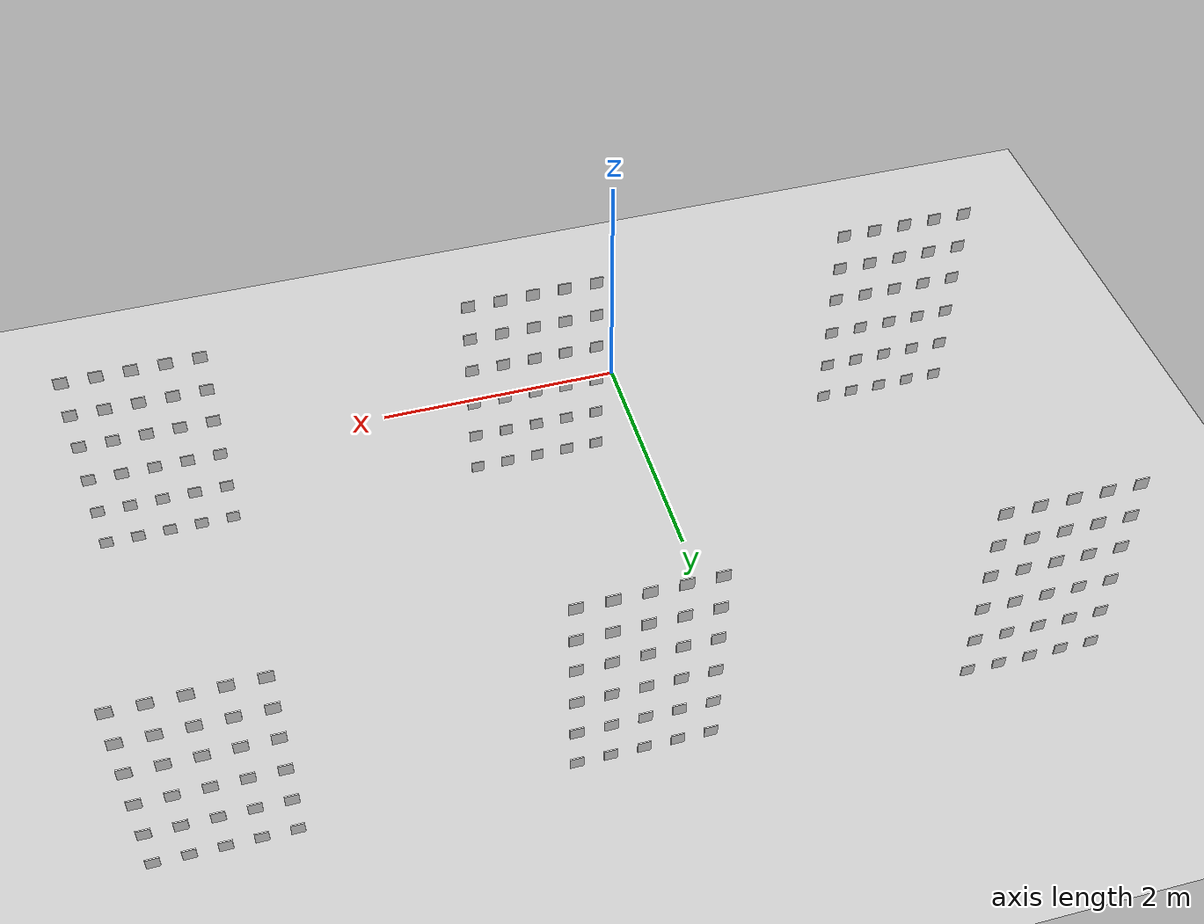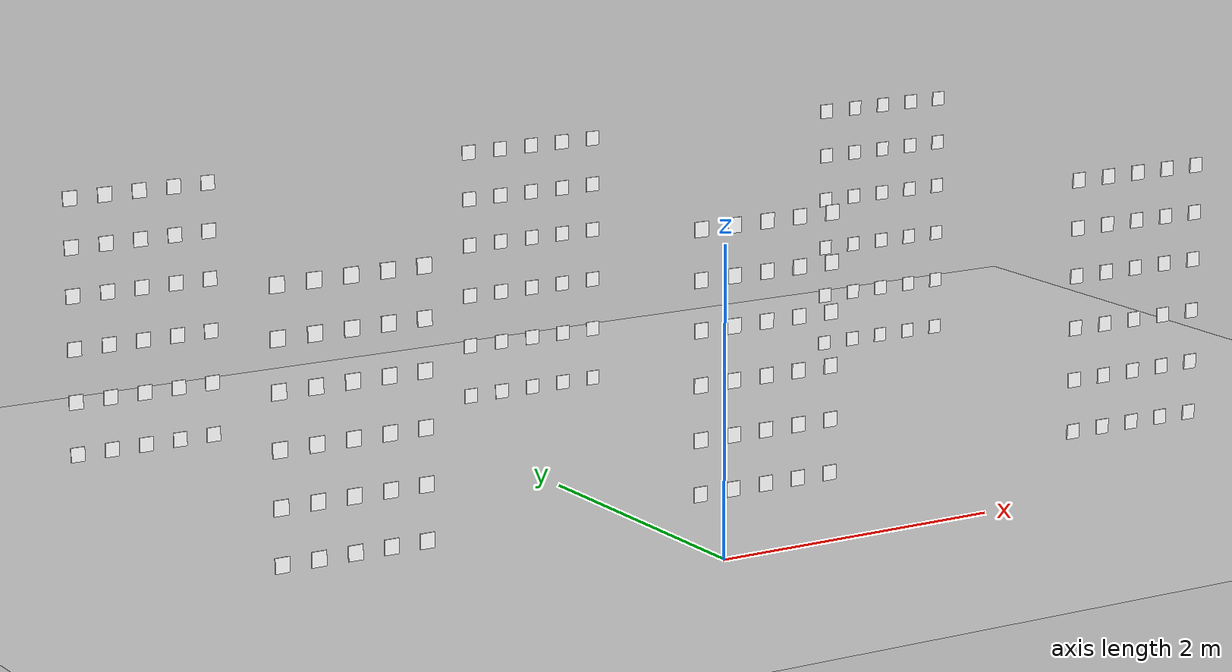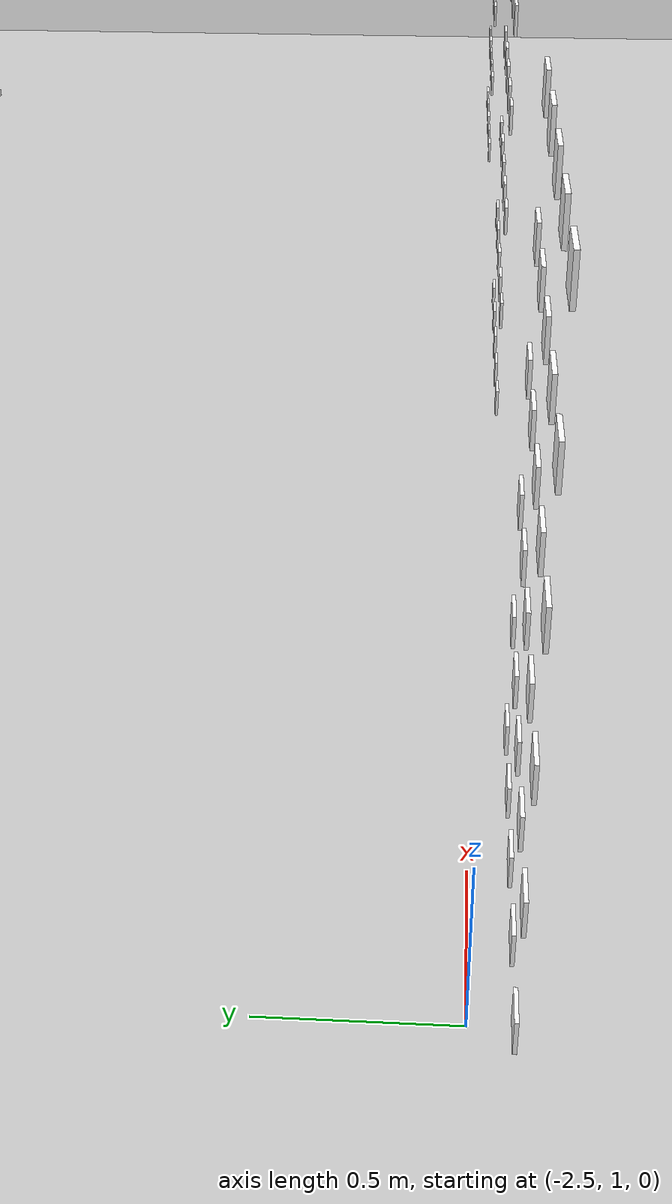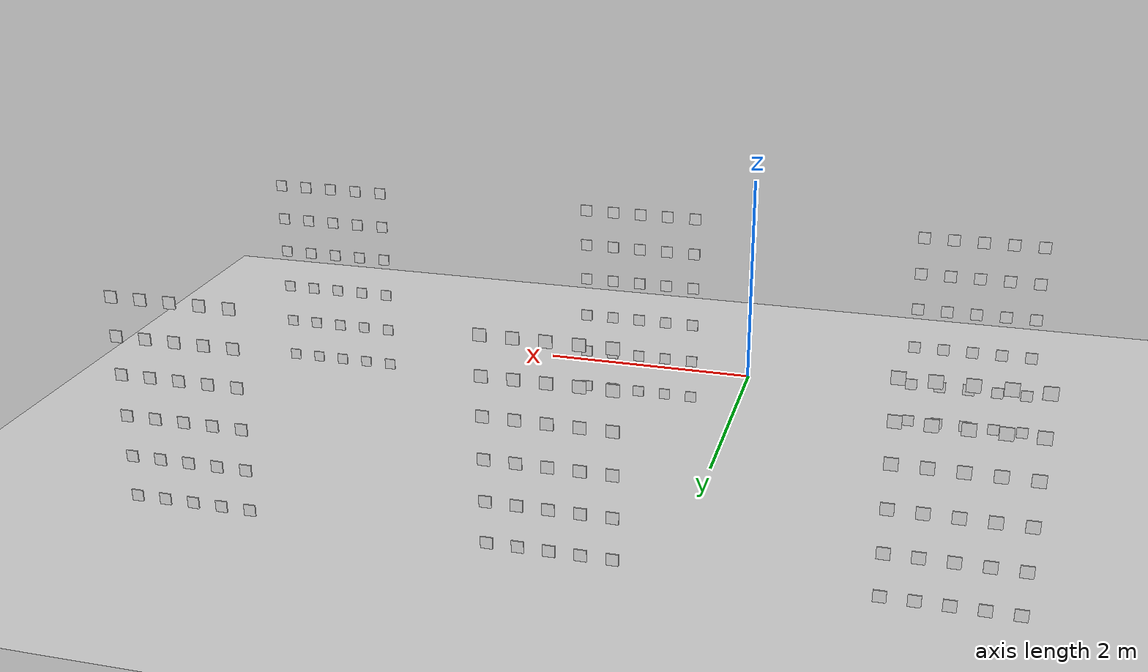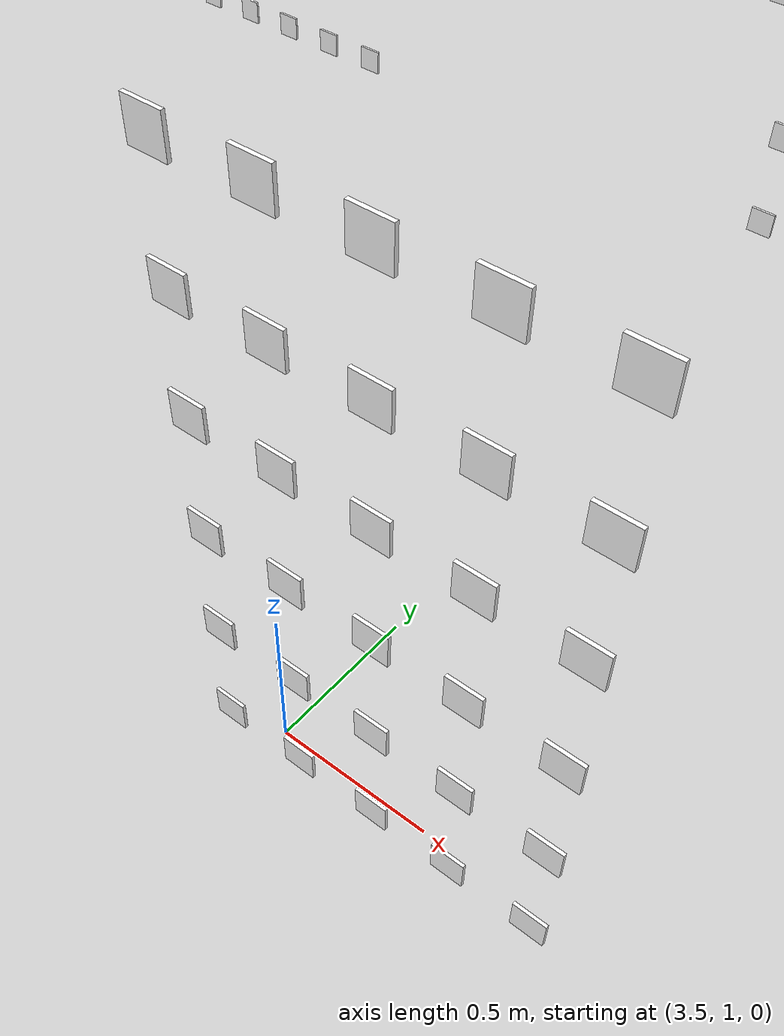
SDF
<sdf version="1.6">
 <world name="default">
  <include><uri>model://ground_plane</uri></include>
  <include><uri>model://sun</uri></include>
  <model name="stag_r1c1_l1_m1">
   <static>true</static>
   <pose>-1.6 0.9 0.146 1.5708 0 0</pose>
   <link name="marker_link">
    <collision name="collision"><geometry><box><size>0.1 0.1 0.01</size></box></geometry></collision>
    <visual name="visual">
     <geometry><box><size>0.1 0.1 0.01</size></box></geometry>
     <material>
      <script>
       <uri>model://STag_marker/materials/scripts</uri>
       <uri>model://STag_marker/materials/textures</uri>
       <name>STagMarker/marker_00219</name>
      </script>
      <ambient>1 1 1 1</ambient>
      <diffuse>1 1 1 1</diffuse>
     </material>
     <pose>0 0 0.001 0 0 0</pose>
    </visual>
   </link>
  </model>
  <model name="stag_r1c1_l1_m2">
   <static>true</static>
   <pose>-1.85 0.9 0.146 1.5708 0 0</pose>
   <link name="marker_link">
    <collision name="collision"><geometry><box><size>0.1 0.1 0.01</size></box></geometry></collision>
    <visual name="visual">
     <geometry><box><size>0.1 0.1 0.01</size></box></geometry>
     <material>
      <script>
       <uri>model://STag_marker/materials/scripts</uri>
       <uri>model://STag_marker/materials/textures</uri>
       <name>STagMarker/marker_00261</name>
      </script>
      <ambient>1 1 1 1</ambient>
      <diffuse>1 1 1 1</diffuse>
     </material>
     <pose>0 0 0.001 0 0 0</pose>
    </visual>
   </link>
  </model>
  <model name="stag_r1c1_l1_m3">
   <static>true</static>
   <pose>-2.1 0.9 0.146 1.5708 0 0</pose>
   <link name="marker_link">
    <collision name="collision"><geometry><box><size>0.1 0.1 0.01</size></box></geometry></collision>
    <visual name="visual">
     <geometry><box><size>0.1 0.1 0.01</size></box></geometry>
     <material>
      <script>
       <uri>model://STag_marker/materials/scripts</uri>
       <uri>model://STag_marker/materials/textures</uri>
       <name>STagMarker/marker_00426</name>
      </script>
      <ambient>1 1 1 1</ambient>
      <diffuse>1 1 1 1</diffuse>
     </material>
     <pose>0 0 0.001 0 0 0</pose>
    </visual>
   </link>
  </model>
  <model name="stag_r1c1_l1_m4">
   <static>true</static>
   <pose>-2.35 0.9 0.146 1.5708 0 0</pose>
   <link name="marker_link">
    <collision name="collision"><geometry><box><size>0.1 0.1 0.01</size></box></geometry></collision>
    <visual name="visual">
     <geometry><box><size>0.1 0.1 0.01</size></box></geometry>
     <material>
      <script>
       <uri>model://STag_marker/materials/scripts</uri>
       <uri>model://STag_marker/materials/textures</uri>
       <name>STagMarker/marker_00519</name>
      </script>
      <ambient>1 1 1 1</ambient>
      <diffuse>1 1 1 1</diffuse>
     </material>
     <pose>0 0 0.001 0 0 0</pose>
    </visual>
   </link>
  </model>
  <model name="stag_r1c1_l1_m5">
   <static>true</static>
   <pose>-2.6 0.9 0.146 1.5708 0 0</pose>
   <link name="marker_link">
    <collision name="collision"><geometry><box><size>0.1 0.1 0.01</size></box></geometry></collision>
    <visual name="visual">
     <geometry><box><size>0.1 0.1 0.01</size></box></geometry>
     <material>
      <script>
       <uri>model://STag_marker/materials/scripts</uri>
       <uri>model://STag_marker/materials/textures</uri>
       <name>STagMarker/marker_00525</name>
      </script>
      <ambient>1 1 1 1</ambient>
      <diffuse>1 1 1 1</diffuse>
     </material>
     <pose>0 0 0.001 0 0 0</pose>
    </visual>
   </link>
  </model>
  <model name="stag_r1c1_l2_m1">
   <static>true</static>
   <pose>-1.6 0.9 0.506 1.5708 0 0</pose>
   <link name="marker_link">
    <collision name="collision"><geometry><box><size>0.1 0.1 0.01</size></box></geometry></collision>
    <visual name="visual">
     <geometry><box><size>0.1 0.1 0.01</size></box></geometry>
     <material>
      <script>
       <uri>model://STag_marker/materials/scripts</uri>
       <uri>model://STag_marker/materials/textures</uri>
       <name>STagMarker/marker_00526</name>
      </script>
      <ambient>1 1 1 1</ambient>
      <diffuse>1 1 1 1</diffuse>
     </material>
     <pose>0 0 0.001 0 0 0</pose>
    </visual>
   </link>
  </model>
  <model name="stag_r1c1_l2_m2">
   <static>true</static>
   <pose>-1.85 0.9 0.506 1.5708 0 0</pose>
   <link name="marker_link">
    <collision name="collision"><geometry><box><size>0.1 0.1 0.01</size></box></geometry></collision>
    <visual name="visual">
     <geometry><box><size>0.1 0.1 0.01</size></box></geometry>
     <material>
      <script>
       <uri>model://STag_marker/materials/scripts</uri>
       <uri>model://STag_marker/materials/textures</uri>
       <name>STagMarker/marker_00537</name>
      </script>
      <ambient>1 1 1 1</ambient>
      <diffuse>1 1 1 1</diffuse>
     </material>
     <pose>0 0 0.001 0 0 0</pose>
    </visual>
   </link>
  </model>
  <model name="stag_r1c1_l2_m3">
   <static>true</static>
   <pose>-2.1 0.9 0.506 1.5708 0 0</pose>
   <link name="marker_link">
    <collision name="collision"><geometry><box><size>0.1 0.1 0.01</size></box></geometry></collision>
    <visual name="visual">
     <geometry><box><size>0.1 0.1 0.01</size></box></geometry>
     <material>
      <script>
       <uri>model://STag_marker/materials/scripts</uri>
       <uri>model://STag_marker/materials/textures</uri>
       <name>STagMarker/marker_00563</name>
      </script>
      <ambient>1 1 1 1</ambient>
      <diffuse>1 1 1 1</diffuse>
     </material>
     <pose>0 0 0.001 0 0 0</pose>
    </visual>
   </link>
  </model>
  <model name="stag_r1c1_l2_m4">
   <static>true</static>
   <pose>-2.35 0.9 0.506 1.5708 0 0</pose>
   <link name="marker_link">
    <collision name="collision"><geometry><box><size>0.1 0.1 0.01</size></box></geometry></collision>
    <visual name="visual">
     <geometry><box><size>0.1 0.1 0.01</size></box></geometry>
     <material>
      <script>
       <uri>model://STag_marker/materials/scripts</uri>
       <uri>model://STag_marker/materials/textures</uri>
       <name>STagMarker/marker_00578</name>
      </script>
      <ambient>1 1 1 1</ambient>
      <diffuse>1 1 1 1</diffuse>
     </material>
     <pose>0 0 0.001 0 0 0</pose>
    </visual>
   </link>
  </model>
  <model name="stag_r1c1_l2_m5">
   <static>true</static>
   <pose>-2.6 0.9 0.506 1.5708 0 0</pose>
   <link name="marker_link">
    <collision name="collision"><geometry><box><size>0.1 0.1 0.01</size></box></geometry></collision>
    <visual name="visual">
     <geometry><box><size>0.1 0.1 0.01</size></box></geometry>
     <material>
      <script>
       <uri>model://STag_marker/materials/scripts</uri>
       <uri>model://STag_marker/materials/textures</uri>
       <name>STagMarker/marker_00679</name>
      </script>
      <ambient>1 1 1 1</ambient>
      <diffuse>1 1 1 1</diffuse>
     </material>
     <pose>0 0 0.001 0 0 0</pose>
    </visual>
   </link>
  </model>
  <model name="stag_r1c1_l3_m1">
   <static>true</static>
   <pose>-1.6 0.9 0.867 1.5708 0 0</pose>
   <link name="marker_link">
    <collision name="collision"><geometry><box><size>0.1 0.1 0.01</size></box></geometry></collision>
    <visual name="visual">
     <geometry><box><size>0.1 0.1 0.01</size></box></geometry>
     <material>
      <script>
       <uri>model://STag_marker/materials/scripts</uri>
       <uri>model://STag_marker/materials/textures</uri>
       <name>STagMarker/marker_00800</name>
      </script>
      <ambient>1 1 1 1</ambient>
      <diffuse>1 1 1 1</diffuse>
     </material>
     <pose>0 0 0.001 0 0 0</pose>
    </visual>
   </link>
  </model>
  <model name="stag_r1c1_l3_m2">
   <static>true</static>
   <pose>-1.85 0.9 0.867 1.5708 0 0</pose>
   <link name="marker_link">
    <collision name="collision"><geometry><box><size>0.1 0.1 0.01</size></box></geometry></collision>
    <visual name="visual">
     <geometry><box><size>0.1 0.1 0.01</size></box></geometry>
     <material>
      <script>
       <uri>model://STag_marker/materials/scripts</uri>
       <uri>model://STag_marker/materials/textures</uri>
       <name>STagMarker/marker_00848</name>
      </script>
      <ambient>1 1 1 1</ambient>
      <diffuse>1 1 1 1</diffuse>
     </material>
     <pose>0 0 0.001 0 0 0</pose>
    </visual>
   </link>
  </model>
  <model name="stag_r1c1_l3_m3">
   <static>true</static>
   <pose>-2.1 0.9 0.867 1.5708 0 0</pose>
   <link name="marker_link">
    <collision name="collision"><geometry><box><size>0.1 0.1 0.01</size></box></geometry></collision>
    <visual name="visual">
     <geometry><box><size>0.1 0.1 0.01</size></box></geometry>
     <material>
      <script>
       <uri>model://STag_marker/materials/scripts</uri>
       <uri>model://STag_marker/materials/textures</uri>
       <name>STagMarker/marker_01138</name>
      </script>
      <ambient>1 1 1 1</ambient>
      <diffuse>1 1 1 1</diffuse>
     </material>
     <pose>0 0 0.001 0 0 0</pose>
    </visual>
   </link>
  </model>
  <model name="stag_r1c1_l3_m4">
   <static>true</static>
   <pose>-2.35 0.9 0.867 1.5708 0 0</pose>
   <link name="marker_link">
    <collision name="collision"><geometry><box><size>0.1 0.1 0.01</size></box></geometry></collision>
    <visual name="visual">
     <geometry><box><size>0.1 0.1 0.01</size></box></geometry>
     <material>
      <script>
       <uri>model://STag_marker/materials/scripts</uri>
       <uri>model://STag_marker/materials/textures</uri>
       <name>STagMarker/marker_01181</name>
      </script>
      <ambient>1 1 1 1</ambient>
      <diffuse>1 1 1 1</diffuse>
     </material>
     <pose>0 0 0.001 0 0 0</pose>
    </visual>
   </link>
  </model>
  <model name="stag_r1c1_l3_m5">
   <static>true</static>
   <pose>-2.6 0.9 0.867 1.5708 0 0</pose>
   <link name="marker_link">
    <collision name="collision"><geometry><box><size>0.1 0.1 0.01</size></box></geometry></collision>
    <visual name="visual">
     <geometry><box><size>0.1 0.1 0.01</size></box></geometry>
     <material>
      <script>
       <uri>model://STag_marker/materials/scripts</uri>
       <uri>model://STag_marker/materials/textures</uri>
       <name>STagMarker/marker_01311</name>
      </script>
      <ambient>1 1 1 1</ambient>
      <diffuse>1 1 1 1</diffuse>
     </material>
     <pose>0 0 0.001 0 0 0</pose>
    </visual>
   </link>
  </model>
  <model name="stag_r1c1_l4_m1">
   <static>true</static>
   <pose>-1.6 0.9 1.227 1.5708 0 0</pose>
   <link name="marker_link">
    <collision name="collision"><geometry><box><size>0.1 0.1 0.01</size></box></geometry></collision>
    <visual name="visual">
     <geometry><box><size>0.1 0.1 0.01</size></box></geometry>
     <material>
      <script>
       <uri>model://STag_marker/materials/scripts</uri>
       <uri>model://STag_marker/materials/textures</uri>
       <name>STagMarker/marker_01391</name>
      </script>
      <ambient>1 1 1 1</ambient>
      <diffuse>1 1 1 1</diffuse>
     </material>
     <pose>0 0 0.001 0 0 0</pose>
    </visual>
   </link>
  </model>
  <model name="stag_r1c1_l4_m2">
   <static>true</static>
   <pose>-1.85 0.9 1.227 1.5708 0 0</pose>
   <link name="marker_link">
    <collision name="collision"><geometry><box><size>0.1 0.1 0.01</size></box></geometry></collision>
    <visual name="visual">
     <geometry><box><size>0.1 0.1 0.01</size></box></geometry>
     <material>
      <script>
       <uri>model://STag_marker/materials/scripts</uri>
       <uri>model://STag_marker/materials/textures</uri>
       <name>STagMarker/marker_01396</name>
      </script>
      <ambient>1 1 1 1</ambient>
      <diffuse>1 1 1 1</diffuse>
     </material>
     <pose>0 0 0.001 0 0 0</pose>
    </visual>
   </link>
  </model>
  <model name="stag_r1c1_l4_m3">
   <static>true</static>
   <pose>-2.1 0.9 1.227 1.5708 0 0</pose>
   <link name="marker_link">
    <collision name="collision"><geometry><box><size>0.1 0.1 0.01</size></box></geometry></collision>
    <visual name="visual">
     <geometry><box><size>0.1 0.1 0.01</size></box></geometry>
     <material>
      <script>
       <uri>model://STag_marker/materials/scripts</uri>
       <uri>model://STag_marker/materials/textures</uri>
       <name>STagMarker/marker_01451</name>
      </script>
      <ambient>1 1 1 1</ambient>
      <diffuse>1 1 1 1</diffuse>
     </material>
     <pose>0 0 0.001 0 0 0</pose>
    </visual>
   </link>
  </model>
  <model name="stag_r1c1_l4_m4">
   <static>true</static>
   <pose>-2.35 0.9 1.227 1.5708 0 0</pose>
   <link name="marker_link">
    <collision name="collision"><geometry><box><size>0.1 0.1 0.01</size></box></geometry></collision>
    <visual name="visual">
     <geometry><box><size>0.1 0.1 0.01</size></box></geometry>
     <material>
      <script>
       <uri>model://STag_marker/materials/scripts</uri>
       <uri>model://STag_marker/materials/textures</uri>
       <name>STagMarker/marker_01509</name>
      </script>
      <ambient>1 1 1 1</ambient>
      <diffuse>1 1 1 1</diffuse>
     </material>
     <pose>0 0 0.001 0 0 0</pose>
    </visual>
   </link>
  </model>
  <model name="stag_r1c1_l4_m5">
   <static>true</static>
   <pose>-2.6 0.9 1.227 1.5708 0 0</pose>
   <link name="marker_link">
    <collision name="collision"><geometry><box><size>0.1 0.1 0.01</size></box></geometry></collision>
    <visual name="visual">
     <geometry><box><size>0.1 0.1 0.01</size></box></geometry>
     <material>
      <script>
       <uri>model://STag_marker/materials/scripts</uri>
       <uri>model://STag_marker/materials/textures</uri>
       <name>STagMarker/marker_01579</name>
      </script>
      <ambient>1 1 1 1</ambient>
      <diffuse>1 1 1 1</diffuse>
     </material>
     <pose>0 0 0.001 0 0 0</pose>
    </visual>
   </link>
  </model>
  <model name="stag_r1c1_l5_m1">
   <static>true</static>
   <pose>-1.6 0.9 1.556 1.5708 0 0</pose>
   <link name="marker_link">
    <collision name="collision"><geometry><box><size>0.1 0.1 0.01</size></box></geometry></collision>
    <visual name="visual">
     <geometry><box><size>0.1 0.1 0.01</size></box></geometry>
     <material>
      <script>
       <uri>model://STag_marker/materials/scripts</uri>
       <uri>model://STag_marker/materials/textures</uri>
       <name>STagMarker/marker_01603</name>
      </script>
      <ambient>1 1 1 1</ambient>
      <diffuse>1 1 1 1</diffuse>
     </material>
     <pose>0 0 0.001 0 0 0</pose>
    </visual>
   </link>
  </model>
  <model name="stag_r1c1_l5_m2">
   <static>true</static>
   <pose>-1.85 0.9 1.556 1.5708 0 0</pose>
   <link name="marker_link">
    <collision name="collision"><geometry><box><size>0.1 0.1 0.01</size></box></geometry></collision>
    <visual name="visual">
     <geometry><box><size>0.1 0.1 0.01</size></box></geometry>
     <material>
      <script>
       <uri>model://STag_marker/materials/scripts</uri>
       <uri>model://STag_marker/materials/textures</uri>
       <name>STagMarker/marker_01630</name>
      </script>
      <ambient>1 1 1 1</ambient>
      <diffuse>1 1 1 1</diffuse>
     </material>
     <pose>0 0 0.001 0 0 0</pose>
    </visual>
   </link>
  </model>
  <model name="stag_r1c1_l5_m3">
   <static>true</static>
   <pose>-2.1 0.9 1.556 1.5708 0 0</pose>
   <link name="marker_link">
    <collision name="collision"><geometry><box><size>0.1 0.1 0.01</size></box></geometry></collision>
    <visual name="visual">
     <geometry><box><size>0.1 0.1 0.01</size></box></geometry>
     <material>
      <script>
       <uri>model://STag_marker/materials/scripts</uri>
       <uri>model://STag_marker/materials/textures</uri>
       <name>STagMarker/marker_01654</name>
      </script>
      <ambient>1 1 1 1</ambient>
      <diffuse>1 1 1 1</diffuse>
     </material>
     <pose>0 0 0.001 0 0 0</pose>
    </visual>
   </link>
  </model>
  <model name="stag_r1c1_l5_m4">
   <static>true</static>
   <pose>-2.35 0.9 1.556 1.5708 0 0</pose>
   <link name="marker_link">
    <collision name="collision"><geometry><box><size>0.1 0.1 0.01</size></box></geometry></collision>
    <visual name="visual">
     <geometry><box><size>0.1 0.1 0.01</size></box></geometry>
     <material>
      <script>
       <uri>model://STag_marker/materials/scripts</uri>
       <uri>model://STag_marker/materials/textures</uri>
       <name>STagMarker/marker_01690</name>
      </script>
      <ambient>1 1 1 1</ambient>
      <diffuse>1 1 1 1</diffuse>
     </material>
     <pose>0 0 0.001 0 0 0</pose>
    </visual>
   </link>
  </model>
  <model name="stag_r1c1_l5_m5">
   <static>true</static>
   <pose>-2.6 0.9 1.556 1.5708 0 0</pose>
   <link name="marker_link">
    <collision name="collision"><geometry><box><size>0.1 0.1 0.01</size></box></geometry></collision>
    <visual name="visual">
     <geometry><box><size>0.1 0.1 0.01</size></box></geometry>
     <material>
      <script>
       <uri>model://STag_marker/materials/scripts</uri>
       <uri>model://STag_marker/materials/textures</uri>
       <name>STagMarker/marker_01824</name>
      </script>
      <ambient>1 1 1 1</ambient>
      <diffuse>1 1 1 1</diffuse>
     </material>
     <pose>0 0 0.001 0 0 0</pose>
    </visual>
   </link>
  </model>
  <model name="stag_r1c1_l6_m1">
   <static>true</static>
   <pose>-1.6 0.9 1.886 1.5708 0 0</pose>
   <link name="marker_link">
    <collision name="collision"><geometry><box><size>0.1 0.1 0.01</size></box></geometry></collision>
    <visual name="visual">
     <geometry><box><size>0.1 0.1 0.01</size></box></geometry>
     <material>
      <script>
       <uri>model://STag_marker/materials/scripts</uri>
       <uri>model://STag_marker/materials/textures</uri>
       <name>STagMarker/marker_01862</name>
      </script>
      <ambient>1 1 1 1</ambient>
      <diffuse>1 1 1 1</diffuse>
     </material>
     <pose>0 0 0.001 0 0 0</pose>
    </visual>
   </link>
  </model>
  <model name="stag_r1c1_l6_m2">
   <static>true</static>
   <pose>-1.85 0.9 1.886 1.5708 0 0</pose>
   <link name="marker_link">
    <collision name="collision"><geometry><box><size>0.1 0.1 0.01</size></box></geometry></collision>
    <visual name="visual">
     <geometry><box><size>0.1 0.1 0.01</size></box></geometry>
     <material>
      <script>
       <uri>model://STag_marker/materials/scripts</uri>
       <uri>model://STag_marker/materials/textures</uri>
       <name>STagMarker/marker_01928</name>
      </script>
      <ambient>1 1 1 1</ambient>
      <diffuse>1 1 1 1</diffuse>
     </material>
     <pose>0 0 0.001 0 0 0</pose>
    </visual>
   </link>
  </model>
  <model name="stag_r1c1_l6_m3">
   <static>true</static>
   <pose>-2.1 0.9 1.886 1.5708 0 0</pose>
   <link name="marker_link">
    <collision name="collision"><geometry><box><size>0.1 0.1 0.01</size></box></geometry></collision>
    <visual name="visual">
     <geometry><box><size>0.1 0.1 0.01</size></box></geometry>
     <material>
      <script>
       <uri>model://STag_marker/materials/scripts</uri>
       <uri>model://STag_marker/materials/textures</uri>
       <name>STagMarker/marker_01999</name>
      </script>
      <ambient>1 1 1 1</ambient>
      <diffuse>1 1 1 1</diffuse>
     </material>
     <pose>0 0 0.001 0 0 0</pose>
    </visual>
   </link>
  </model>
  <model name="stag_r1c1_l6_m4">
   <static>true</static>
   <pose>-2.35 0.9 1.886 1.5708 0 0</pose>
   <link name="marker_link">
    <collision name="collision"><geometry><box><size>0.1 0.1 0.01</size></box></geometry></collision>
    <visual name="visual">
     <geometry><box><size>0.1 0.1 0.01</size></box></geometry>
     <material>
      <script>
       <uri>model://STag_marker/materials/scripts</uri>
       <uri>model://STag_marker/materials/textures</uri>
       <name>STagMarker/marker_02027</name>
      </script>
      <ambient>1 1 1 1</ambient>
      <diffuse>1 1 1 1</diffuse>
     </material>
     <pose>0 0 0.001 0 0 0</pose>
    </visual>
   </link>
  </model>
  <model name="stag_r1c1_l6_m5">
   <static>true</static>
   <pose>-2.6 0.9 1.886 1.5708 0 0</pose>
   <link name="marker_link">
    <collision name="collision"><geometry><box><size>0.1 0.1 0.01</size></box></geometry></collision>
    <visual name="visual">
     <geometry><box><size>0.1 0.1 0.01</size></box></geometry>
     <material>
      <script>
       <uri>model://STag_marker/materials/scripts</uri>
       <uri>model://STag_marker/materials/textures</uri>
       <name>STagMarker/marker_02149</name>
      </script>
      <ambient>1 1 1 1</ambient>
      <diffuse>1 1 1 1</diffuse>
     </material>
     <pose>0 0 0.001 0 0 0</pose>
    </visual>
   </link>
  </model>
  <model name="stag_r1c2_l1_m1">
   <static>true</static>
   <pose>1.4 0.9 0.146 1.5708 0 0</pose>
   <link name="marker_link">
    <collision name="collision"><geometry><box><size>0.1 0.1 0.01</size></box></geometry></collision>
    <visual name="visual">
     <geometry><box><size>0.1 0.1 0.01</size></box></geometry>
     <material>
      <script>
       <uri>model://STag_marker/materials/scripts</uri>
       <uri>model://STag_marker/materials/textures</uri>
       <name>STagMarker/marker_02234</name>
      </script>
      <ambient>1 1 1 1</ambient>
      <diffuse>1 1 1 1</diffuse>
     </material>
     <pose>0 0 0.001 0 0 0</pose>
    </visual>
   </link>
  </model>
  <model name="stag_r1c2_l1_m2">
   <static>true</static>
   <pose>1.15 0.9 0.146 1.5708 0 0</pose>
   <link name="marker_link">
    <collision name="collision"><geometry><box><size>0.1 0.1 0.01</size></box></geometry></collision>
    <visual name="visual">
     <geometry><box><size>0.1 0.1 0.01</size></box></geometry>
     <material>
      <script>
       <uri>model://STag_marker/materials/scripts</uri>
       <uri>model://STag_marker/materials/textures</uri>
       <name>STagMarker/marker_02269</name>
      </script>
      <ambient>1 1 1 1</ambient>
      <diffuse>1 1 1 1</diffuse>
     </material>
     <pose>0 0 0.001 0 0 0</pose>
    </visual>
   </link>
  </model>
  <model name="stag_r1c2_l1_m3">
   <static>true</static>
   <pose>0.8999999999999999 0.9 0.146 1.5708 0 0</pose>
   <link name="marker_link">
    <collision name="collision"><geometry><box><size>0.1 0.1 0.01</size></box></geometry></collision>
    <visual name="visual">
     <geometry><box><size>0.1 0.1 0.01</size></box></geometry>
     <material>
      <script>
       <uri>model://STag_marker/materials/scripts</uri>
       <uri>model://STag_marker/materials/textures</uri>
       <name>STagMarker/marker_02275</name>
      </script>
      <ambient>1 1 1 1</ambient>
      <diffuse>1 1 1 1</diffuse>
     </material>
     <pose>0 0 0.001 0 0 0</pose>
    </visual>
   </link>
  </model>
  <model name="stag_r1c2_l1_m4">
   <static>true</static>
   <pose>0.6499999999999999 0.9 0.146 1.5708 0 0</pose>
   <link name="marker_link">
    <collision name="collision"><geometry><box><size>0.1 0.1 0.01</size></box></geometry></collision>
    <visual name="visual">
     <geometry><box><size>0.1 0.1 0.01</size></box></geometry>
     <material>
      <script>
       <uri>model://STag_marker/materials/scripts</uri>
       <uri>model://STag_marker/materials/textures</uri>
       <name>STagMarker/marker_02288</name>
      </script>
      <ambient>1 1 1 1</ambient>
      <diffuse>1 1 1 1</diffuse>
     </material>
     <pose>0 0 0.001 0 0 0</pose>
    </visual>
   </link>
  </model>
  <model name="stag_r1c2_l1_m5">
   <static>true</static>
   <pose>0.3999999999999999 0.9 0.146 1.5708 0 0</pose>
   <link name="marker_link">
    <collision name="collision"><geometry><box><size>0.1 0.1 0.01</size></box></geometry></collision>
    <visual name="visual">
     <geometry><box><size>0.1 0.1 0.01</size></box></geometry>
     <material>
      <script>
       <uri>model://STag_marker/materials/scripts</uri>
       <uri>model://STag_marker/materials/textures</uri>
       <name>STagMarker/marker_02346</name>
      </script>
      <ambient>1 1 1 1</ambient>
      <diffuse>1 1 1 1</diffuse>
     </material>
     <pose>0 0 0.001 0 0 0</pose>
    </visual>
   </link>
  </model>
  <model name="stag_r1c2_l2_m1">
   <static>true</static>
   <pose>1.4 0.9 0.506 1.5708 0 0</pose>
   <link name="marker_link">
    <collision name="collision"><geometry><box><size>0.1 0.1 0.01</size></box></geometry></collision>
    <visual name="visual">
     <geometry><box><size>0.1 0.1 0.01</size></box></geometry>
     <material>
      <script>
       <uri>model://STag_marker/materials/scripts</uri>
       <uri>model://STag_marker/materials/textures</uri>
       <name>STagMarker/marker_02365</name>
      </script>
      <ambient>1 1 1 1</ambient>
      <diffuse>1 1 1 1</diffuse>
     </material>
     <pose>0 0 0.001 0 0 0</pose>
    </visual>
   </link>
  </model>
  <model name="stag_r1c2_l2_m2">
   <static>true</static>
   <pose>1.15 0.9 0.506 1.5708 0 0</pose>
   <link name="marker_link">
    <collision name="collision"><geometry><box><size>0.1 0.1 0.01</size></box></geometry></collision>
    <visual name="visual">
     <geometry><box><size>0.1 0.1 0.01</size></box></geometry>
     <material>
      <script>
       <uri>model://STag_marker/materials/scripts</uri>
       <uri>model://STag_marker/materials/textures</uri>
       <name>STagMarker/marker_00219</name>
      </script>
      <ambient>1 1 1 1</ambient>
      <diffuse>1 1 1 1</diffuse>
     </material>
     <pose>0 0 0.001 0 0 0</pose>
    </visual>
   </link>
  </model>
  <model name="stag_r1c2_l2_m3">
   <static>true</static>
   <pose>0.8999999999999999 0.9 0.506 1.5708 0 0</pose>
   <link name="marker_link">
    <collision name="collision"><geometry><box><size>0.1 0.1 0.01</size></box></geometry></collision>
    <visual name="visual">
     <geometry><box><size>0.1 0.1 0.01</size></box></geometry>
     <material>
      <script>
       <uri>model://STag_marker/materials/scripts</uri>
       <uri>model://STag_marker/materials/textures</uri>
       <name>STagMarker/marker_00261</name>
      </script>
      <ambient>1 1 1 1</ambient>
      <diffuse>1 1 1 1</diffuse>
     </material>
     <pose>0 0 0.001 0 0 0</pose>
    </visual>
   </link>
  </model>
  <model name="stag_r1c2_l2_m4">
   <static>true</static>
   <pose>0.6499999999999999 0.9 0.506 1.5708 0 0</pose>
   <link name="marker_link">
    <collision name="collision"><geometry><box><size>0.1 0.1 0.01</size></box></geometry></collision>
    <visual name="visual">
     <geometry><box><size>0.1 0.1 0.01</size></box></geometry>
     <material>
      <script>
       <uri>model://STag_marker/materials/scripts</uri>
       <uri>model://STag_marker/materials/textures</uri>
       <name>STagMarker/marker_00426</name>
      </script>
      <ambient>1 1 1 1</ambient>
      <diffuse>1 1 1 1</diffuse>
     </material>
     <pose>0 0 0.001 0 0 0</pose>
    </visual>
   </link>
  </model>
  <model name="stag_r1c2_l2_m5">
   <static>true</static>
   <pose>0.3999999999999999 0.9 0.506 1.5708 0 0</pose>
   <link name="marker_link">
    <collision name="collision"><geometry><box><size>0.1 0.1 0.01</size></box></geometry></collision>
    <visual name="visual">
     <geometry><box><size>0.1 0.1 0.01</size></box></geometry>
     <material>
      <script>
       <uri>model://STag_marker/materials/scripts</uri>
       <uri>model://STag_marker/materials/textures</uri>
       <name>STagMarker/marker_00519</name>
      </script>
      <ambient>1 1 1 1</ambient>
      <diffuse>1 1 1 1</diffuse>
     </material>
     <pose>0 0 0.001 0 0 0</pose>
    </visual>
   </link>
  </model>
  <model name="stag_r1c2_l3_m1">
   <static>true</static>
   <pose>1.4 0.9 0.867 1.5708 0 0</pose>
   <link name="marker_link">
    <collision name="collision"><geometry><box><size>0.1 0.1 0.01</size></box></geometry></collision>
    <visual name="visual">
     <geometry><box><size>0.1 0.1 0.01</size></box></geometry>
     <material>
      <script>
       <uri>model://STag_marker/materials/scripts</uri>
       <uri>model://STag_marker/materials/textures</uri>
       <name>STagMarker/marker_00525</name>
      </script>
      <ambient>1 1 1 1</ambient>
      <diffuse>1 1 1 1</diffuse>
     </material>
     <pose>0 0 0.001 0 0 0</pose>
    </visual>
   </link>
  </model>
  <model name="stag_r1c2_l3_m2">
   <static>true</static>
   <pose>1.15 0.9 0.867 1.5708 0 0</pose>
   <link name="marker_link">
    <collision name="collision"><geometry><box><size>0.1 0.1 0.01</size></box></geometry></collision>
    <visual name="visual">
     <geometry><box><size>0.1 0.1 0.01</size></box></geometry>
     <material>
      <script>
       <uri>model://STag_marker/materials/scripts</uri>
       <uri>model://STag_marker/materials/textures</uri>
       <name>STagMarker/marker_00526</name>
      </script>
      <ambient>1 1 1 1</ambient>
      <diffuse>1 1 1 1</diffuse>
     </material>
     <pose>0 0 0.001 0 0 0</pose>
    </visual>
   </link>
  </model>
  <model name="stag_r1c2_l3_m3">
   <static>true</static>
   <pose>0.8999999999999999 0.9 0.867 1.5708 0 0</pose>
   <link name="marker_link">
    <collision name="collision"><geometry><box><size>0.1 0.1 0.01</size></box></geometry></collision>
    <visual name="visual">
     <geometry><box><size>0.1 0.1 0.01</size></box></geometry>
     <material>
      <script>
       <uri>model://STag_marker/materials/scripts</uri>
       <uri>model://STag_marker/materials/textures</uri>
       <name>STagMarker/marker_00537</name>
      </script>
      <ambient>1 1 1 1</ambient>
      <diffuse>1 1 1 1</diffuse>
     </material>
     <pose>0 0 0.001 0 0 0</pose>
    </visual>
   </link>
  </model>
  <model name="stag_r1c2_l3_m4">
   <static>true</static>
   <pose>0.6499999999999999 0.9 0.867 1.5708 0 0</pose>
   <link name="marker_link">
    <collision name="collision"><geometry><box><size>0.1 0.1 0.01</size></box></geometry></collision>
    <visual name="visual">
     <geometry><box><size>0.1 0.1 0.01</size></box></geometry>
     <material>
      <script>
       <uri>model://STag_marker/materials/scripts</uri>
       <uri>model://STag_marker/materials/textures</uri>
       <name>STagMarker/marker_00563</name>
      </script>
      <ambient>1 1 1 1</ambient>
      <diffuse>1 1 1 1</diffuse>
     </material>
     <pose>0 0 0.001 0 0 0</pose>
    </visual>
   </link>
  </model>
  <model name="stag_r1c2_l3_m5">
   <static>true</static>
   <pose>0.3999999999999999 0.9 0.867 1.5708 0 0</pose>
   <link name="marker_link">
    <collision name="collision"><geometry><box><size>0.1 0.1 0.01</size></box></geometry></collision>
    <visual name="visual">
     <geometry><box><size>0.1 0.1 0.01</size></box></geometry>
     <material>
      <script>
       <uri>model://STag_marker/materials/scripts</uri>
       <uri>model://STag_marker/materials/textures</uri>
       <name>STagMarker/marker_00578</name>
      </script>
      <ambient>1 1 1 1</ambient>
      <diffuse>1 1 1 1</diffuse>
     </material>
     <pose>0 0 0.001 0 0 0</pose>
    </visual>
   </link>
  </model>
  <model name="stag_r1c2_l4_m1">
   <static>true</static>
   <pose>1.4 0.9 1.227 1.5708 0 0</pose>
   <link name="marker_link">
    <collision name="collision"><geometry><box><size>0.1 0.1 0.01</size></box></geometry></collision>
    <visual name="visual">
     <geometry><box><size>0.1 0.1 0.01</size></box></geometry>
     <material>
      <script>
       <uri>model://STag_marker/materials/scripts</uri>
       <uri>model://STag_marker/materials/textures</uri>
       <name>STagMarker/marker_00679</name>
      </script>
      <ambient>1 1 1 1</ambient>
      <diffuse>1 1 1 1</diffuse>
     </material>
     <pose>0 0 0.001 0 0 0</pose>
    </visual>
   </link>
  </model>
  <model name="stag_r1c2_l4_m2">
   <static>true</static>
   <pose>1.15 0.9 1.227 1.5708 0 0</pose>
   <link name="marker_link">
    <collision name="collision"><geometry><box><size>0.1 0.1 0.01</size></box></geometry></collision>
    <visual name="visual">
     <geometry><box><size>0.1 0.1 0.01</size></box></geometry>
     <material>
      <script>
       <uri>model://STag_marker/materials/scripts</uri>
       <uri>model://STag_marker/materials/textures</uri>
       <name>STagMarker/marker_00800</name>
      </script>
      <ambient>1 1 1 1</ambient>
      <diffuse>1 1 1 1</diffuse>
     </material>
     <pose>0 0 0.001 0 0 0</pose>
    </visual>
   </link>
  </model>
  <model name="stag_r1c2_l4_m3">
   <static>true</static>
   <pose>0.8999999999999999 0.9 1.227 1.5708 0 0</pose>
   <link name="marker_link">
    <collision name="collision"><geometry><box><size>0.1 0.1 0.01</size></box></geometry></collision>
    <visual name="visual">
     <geometry><box><size>0.1 0.1 0.01</size></box></geometry>
     <material>
      <script>
       <uri>model://STag_marker/materials/scripts</uri>
       <uri>model://STag_marker/materials/textures</uri>
       <name>STagMarker/marker_00848</name>
      </script>
      <ambient>1 1 1 1</ambient>
      <diffuse>1 1 1 1</diffuse>
     </material>
     <pose>0 0 0.001 0 0 0</pose>
    </visual>
   </link>
  </model>
  <model name="stag_r1c2_l4_m4">
   <static>true</static>
   <pose>0.6499999999999999 0.9 1.227 1.5708 0 0</pose>
   <link name="marker_link">
    <collision name="collision"><geometry><box><size>0.1 0.1 0.01</size></box></geometry></collision>
    <visual name="visual">
     <geometry><box><size>0.1 0.1 0.01</size></box></geometry>
     <material>
      <script>
       <uri>model://STag_marker/materials/scripts</uri>
       <uri>model://STag_marker/materials/textures</uri>
       <name>STagMarker/marker_01138</name>
      </script>
      <ambient>1 1 1 1</ambient>
      <diffuse>1 1 1 1</diffuse>
     </material>
     <pose>0 0 0.001 0 0 0</pose>
    </visual>
   </link>
  </model>
  <model name="stag_r1c2_l4_m5">
   <static>true</static>
   <pose>0.3999999999999999 0.9 1.227 1.5708 0 0</pose>
   <link name="marker_link">
    <collision name="collision"><geometry><box><size>0.1 0.1 0.01</size></box></geometry></collision>
    <visual name="visual">
     <geometry><box><size>0.1 0.1 0.01</size></box></geometry>
     <material>
      <script>
       <uri>model://STag_marker/materials/scripts</uri>
       <uri>model://STag_marker/materials/textures</uri>
       <name>STagMarker/marker_01181</name>
      </script>
      <ambient>1 1 1 1</ambient>
      <diffuse>1 1 1 1</diffuse>
     </material>
     <pose>0 0 0.001 0 0 0</pose>
    </visual>
   </link>
  </model>
  <model name="stag_r1c2_l5_m1">
   <static>true</static>
   <pose>1.4 0.9 1.556 1.5708 0 0</pose>
   <link name="marker_link">
    <collision name="collision"><geometry><box><size>0.1 0.1 0.01</size></box></geometry></collision>
    <visual name="visual">
     <geometry><box><size>0.1 0.1 0.01</size></box></geometry>
     <material>
      <script>
       <uri>model://STag_marker/materials/scripts</uri>
       <uri>model://STag_marker/materials/textures</uri>
       <name>STagMarker/marker_01311</name>
      </script>
      <ambient>1 1 1 1</ambient>
      <diffuse>1 1 1 1</diffuse>
     </material>
     <pose>0 0 0.001 0 0 0</pose>
    </visual>
   </link>
  </model>
  <model name="stag_r1c2_l5_m2">
   <static>true</static>
   <pose>1.15 0.9 1.556 1.5708 0 0</pose>
   <link name="marker_link">
    <collision name="collision"><geometry><box><size>0.1 0.1 0.01</size></box></geometry></collision>
    <visual name="visual">
     <geometry><box><size>0.1 0.1 0.01</size></box></geometry>
     <material>
      <script>
       <uri>model://STag_marker/materials/scripts</uri>
       <uri>model://STag_marker/materials/textures</uri>
       <name>STagMarker/marker_01391</name>
      </script>
      <ambient>1 1 1 1</ambient>
      <diffuse>1 1 1 1</diffuse>
     </material>
     <pose>0 0 0.001 0 0 0</pose>
    </visual>
   </link>
  </model>
  <model name="stag_r1c2_l5_m3">
   <static>true</static>
   <pose>0.8999999999999999 0.9 1.556 1.5708 0 0</pose>
   <link name="marker_link">
    <collision name="collision"><geometry><box><size>0.1 0.1 0.01</size></box></geometry></collision>
    <visual name="visual">
     <geometry><box><size>0.1 0.1 0.01</size></box></geometry>
     <material>
      <script>
       <uri>model://STag_marker/materials/scripts</uri>
       <uri>model://STag_marker/materials/textures</uri>
       <name>STagMarker/marker_01396</name>
      </script>
      <ambient>1 1 1 1</ambient>
      <diffuse>1 1 1 1</diffuse>
     </material>
     <pose>0 0 0.001 0 0 0</pose>
    </visual>
   </link>
  </model>
  <model name="stag_r1c2_l5_m4">
   <static>true</static>
   <pose>0.6499999999999999 0.9 1.556 1.5708 0 0</pose>
   <link name="marker_link">
    <collision name="collision"><geometry><box><size>0.1 0.1 0.01</size></box></geometry></collision>
    <visual name="visual">
     <geometry><box><size>0.1 0.1 0.01</size></box></geometry>
     <material>
      <script>
       <uri>model://STag_marker/materials/scripts</uri>
       <uri>model://STag_marker/materials/textures</uri>
       <name>STagMarker/marker_01451</name>
      </script>
      <ambient>1 1 1 1</ambient>
      <diffuse>1 1 1 1</diffuse>
     </material>
     <pose>0 0 0.001 0 0 0</pose>
    </visual>
   </link>
  </model>
  <model name="stag_r1c2_l5_m5">
   <static>true</static>
   <pose>0.3999999999999999 0.9 1.556 1.5708 0 0</pose>
   <link name="marker_link">
    <collision name="collision"><geometry><box><size>0.1 0.1 0.01</size></box></geometry></collision>
    <visual name="visual">
     <geometry><box><size>0.1 0.1 0.01</size></box></geometry>
     <material>
      <script>
       <uri>model://STag_marker/materials/scripts</uri>
       <uri>model://STag_marker/materials/textures</uri>
       <name>STagMarker/marker_01509</name>
      </script>
      <ambient>1 1 1 1</ambient>
      <diffuse>1 1 1 1</diffuse>
     </material>
     <pose>0 0 0.001 0 0 0</pose>
    </visual>
   </link>
  </model>
  <model name="stag_r1c2_l6_m1">
   <static>true</static>
   <pose>1.4 0.9 1.886 1.5708 0 0</pose>
   <link name="marker_link">
    <collision name="collision"><geometry><box><size>0.1 0.1 0.01</size></box></geometry></collision>
    <visual name="visual">
     <geometry><box><size>0.1 0.1 0.01</size></box></geometry>
     <material>
      <script>
       <uri>model://STag_marker/materials/scripts</uri>
       <uri>model://STag_marker/materials/textures</uri>
       <name>STagMarker/marker_01579</name>
      </script>
      <ambient>1 1 1 1</ambient>
      <diffuse>1 1 1 1</diffuse>
     </material>
     <pose>0 0 0.001 0 0 0</pose>
    </visual>
   </link>
  </model>
  <model name="stag_r1c2_l6_m2">
   <static>true</static>
   <pose>1.15 0.9 1.886 1.5708 0 0</pose>
   <link name="marker_link">
    <collision name="collision"><geometry><box><size>0.1 0.1 0.01</size></box></geometry></collision>
    <visual name="visual">
     <geometry><box><size>0.1 0.1 0.01</size></box></geometry>
     <material>
      <script>
       <uri>model://STag_marker/materials/scripts</uri>
       <uri>model://STag_marker/materials/textures</uri>
       <name>STagMarker/marker_01603</name>
      </script>
      <ambient>1 1 1 1</ambient>
      <diffuse>1 1 1 1</diffuse>
     </material>
     <pose>0 0 0.001 0 0 0</pose>
    </visual>
   </link>
  </model>
  <model name="stag_r1c2_l6_m3">
   <static>true</static>
   <pose>0.8999999999999999 0.9 1.886 1.5708 0 0</pose>
   <link name="marker_link">
    <collision name="collision"><geometry><box><size>0.1 0.1 0.01</size></box></geometry></collision>
    <visual name="visual">
     <geometry><box><size>0.1 0.1 0.01</size></box></geometry>
     <material>
      <script>
       <uri>model://STag_marker/materials/scripts</uri>
       <uri>model://STag_marker/materials/textures</uri>
       <name>STagMarker/marker_01630</name>
      </script>
      <ambient>1 1 1 1</ambient>
      <diffuse>1 1 1 1</diffuse>
     </material>
     <pose>0 0 0.001 0 0 0</pose>
    </visual>
   </link>
  </model>
  <model name="stag_r1c2_l6_m4">
   <static>true</static>
   <pose>0.6499999999999999 0.9 1.886 1.5708 0 0</pose>
   <link name="marker_link">
    <collision name="collision"><geometry><box><size>0.1 0.1 0.01</size></box></geometry></collision>
    <visual name="visual">
     <geometry><box><size>0.1 0.1 0.01</size></box></geometry>
     <material>
      <script>
       <uri>model://STag_marker/materials/scripts</uri>
       <uri>model://STag_marker/materials/textures</uri>
       <name>STagMarker/marker_01654</name>
      </script>
      <ambient>1 1 1 1</ambient>
      <diffuse>1 1 1 1</diffuse>
     </material>
     <pose>0 0 0.001 0 0 0</pose>
    </visual>
   </link>
  </model>
  <model name="stag_r1c2_l6_m5">
   <static>true</static>
   <pose>0.3999999999999999 0.9 1.886 1.5708 0 0</pose>
   <link name="marker_link">
    <collision name="collision"><geometry><box><size>0.1 0.1 0.01</size></box></geometry></collision>
    <visual name="visual">
     <geometry><box><size>0.1 0.1 0.01</size></box></geometry>
     <material>
      <script>
       <uri>model://STag_marker/materials/scripts</uri>
       <uri>model://STag_marker/materials/textures</uri>
       <name>STagMarker/marker_01690</name>
      </script>
      <ambient>1 1 1 1</ambient>
      <diffuse>1 1 1 1</diffuse>
     </material>
     <pose>0 0 0.001 0 0 0</pose>
    </visual>
   </link>
  </model>
  <model name="stag_r1c3_l1_m1">
   <static>true</static>
   <pose>4.4 0.9 0.146 1.5708 0 0</pose>
   <link name="marker_link">
    <collision name="collision"><geometry><box><size>0.1 0.1 0.01</size></box></geometry></collision>
    <visual name="visual">
     <geometry><box><size>0.1 0.1 0.01</size></box></geometry>
     <material>
      <script>
       <uri>model://STag_marker/materials/scripts</uri>
       <uri>model://STag_marker/materials/textures</uri>
       <name>STagMarker/marker_01824</name>
      </script>
      <ambient>1 1 1 1</ambient>
      <diffuse>1 1 1 1</diffuse>
     </material>
     <pose>0 0 0.001 0 0 0</pose>
    </visual>
   </link>
  </model>
  <model name="stag_r1c3_l1_m2">
   <static>true</static>
   <pose>4.15 0.9 0.146 1.5708 0 0</pose>
   <link name="marker_link">
    <collision name="collision"><geometry><box><size>0.1 0.1 0.01</size></box></geometry></collision>
    <visual name="visual">
     <geometry><box><size>0.1 0.1 0.01</size></box></geometry>
     <material>
      <script>
       <uri>model://STag_marker/materials/scripts</uri>
       <uri>model://STag_marker/materials/textures</uri>
       <name>STagMarker/marker_01862</name>
      </script>
      <ambient>1 1 1 1</ambient>
      <diffuse>1 1 1 1</diffuse>
     </material>
     <pose>0 0 0.001 0 0 0</pose>
    </visual>
   </link>
  </model>
  <model name="stag_r1c3_l1_m3">
   <static>true</static>
   <pose>3.9000000000000004 0.9 0.146 1.5708 0 0</pose>
   <link name="marker_link">
    <collision name="collision"><geometry><box><size>0.1 0.1 0.01</size></box></geometry></collision>
    <visual name="visual">
     <geometry><box><size>0.1 0.1 0.01</size></box></geometry>
     <material>
      <script>
       <uri>model://STag_marker/materials/scripts</uri>
       <uri>model://STag_marker/materials/textures</uri>
       <name>STagMarker/marker_01928</name>
      </script>
      <ambient>1 1 1 1</ambient>
      <diffuse>1 1 1 1</diffuse>
     </material>
     <pose>0 0 0.001 0 0 0</pose>
    </visual>
   </link>
  </model>
  <model name="stag_r1c3_l1_m4">
   <static>true</static>
   <pose>3.6500000000000004 0.9 0.146 1.5708 0 0</pose>
   <link name="marker_link">
    <collision name="collision"><geometry><box><size>0.1 0.1 0.01</size></box></geometry></collision>
    <visual name="visual">
     <geometry><box><size>0.1 0.1 0.01</size></box></geometry>
     <material>
      <script>
       <uri>model://STag_marker/materials/scripts</uri>
       <uri>model://STag_marker/materials/textures</uri>
       <name>STagMarker/marker_01999</name>
      </script>
      <ambient>1 1 1 1</ambient>
      <diffuse>1 1 1 1</diffuse>
     </material>
     <pose>0 0 0.001 0 0 0</pose>
    </visual>
   </link>
  </model>
  <model name="stag_r1c3_l1_m5">
   <static>true</static>
   <pose>3.4000000000000004 0.9 0.146 1.5708 0 0</pose>
   <link name="marker_link">
    <collision name="collision"><geometry><box><size>0.1 0.1 0.01</size></box></geometry></collision>
    <visual name="visual">
     <geometry><box><size>0.1 0.1 0.01</size></box></geometry>
     <material>
      <script>
       <uri>model://STag_marker/materials/scripts</uri>
       <uri>model://STag_marker/materials/textures</uri>
       <name>STagMarker/marker_02027</name>
      </script>
      <ambient>1 1 1 1</ambient>
      <diffuse>1 1 1 1</diffuse>
     </material>
     <pose>0 0 0.001 0 0 0</pose>
    </visual>
   </link>
  </model>
  <model name="stag_r1c3_l2_m1">
   <static>true</static>
   <pose>4.4 0.9 0.506 1.5708 0 0</pose>
   <link name="marker_link">
    <collision name="collision"><geometry><box><size>0.1 0.1 0.01</size></box></geometry></collision>
    <visual name="visual">
     <geometry><box><size>0.1 0.1 0.01</size></box></geometry>
     <material>
      <script>
       <uri>model://STag_marker/materials/scripts</uri>
       <uri>model://STag_marker/materials/textures</uri>
       <name>STagMarker/marker_02149</name>
      </script>
      <ambient>1 1 1 1</ambient>
      <diffuse>1 1 1 1</diffuse>
     </material>
     <pose>0 0 0.001 0 0 0</pose>
    </visual>
   </link>
  </model>
  <model name="stag_r1c3_l2_m2">
   <static>true</static>
   <pose>4.15 0.9 0.506 1.5708 0 0</pose>
   <link name="marker_link">
    <collision name="collision"><geometry><box><size>0.1 0.1 0.01</size></box></geometry></collision>
    <visual name="visual">
     <geometry><box><size>0.1 0.1 0.01</size></box></geometry>
     <material>
      <script>
       <uri>model://STag_marker/materials/scripts</uri>
       <uri>model://STag_marker/materials/textures</uri>
       <name>STagMarker/marker_02234</name>
      </script>
      <ambient>1 1 1 1</ambient>
      <diffuse>1 1 1 1</diffuse>
     </material>
     <pose>0 0 0.001 0 0 0</pose>
    </visual>
   </link>
  </model>
  <model name="stag_r1c3_l2_m3">
   <static>true</static>
   <pose>3.9000000000000004 0.9 0.506 1.5708 0 0</pose>
   <link name="marker_link">
    <collision name="collision"><geometry><box><size>0.1 0.1 0.01</size></box></geometry></collision>
    <visual name="visual">
     <geometry><box><size>0.1 0.1 0.01</size></box></geometry>
     <material>
      <script>
       <uri>model://STag_marker/materials/scripts</uri>
       <uri>model://STag_marker/materials/textures</uri>
       <name>STagMarker/marker_02269</name>
      </script>
      <ambient>1 1 1 1</ambient>
      <diffuse>1 1 1 1</diffuse>
     </material>
     <pose>0 0 0.001 0 0 0</pose>
    </visual>
   </link>
  </model>
  <model name="stag_r1c3_l2_m4">
   <static>true</static>
   <pose>3.6500000000000004 0.9 0.506 1.5708 0 0</pose>
   <link name="marker_link">
    <collision name="collision"><geometry><box><size>0.1 0.1 0.01</size></box></geometry></collision>
    <visual name="visual">
     <geometry><box><size>0.1 0.1 0.01</size></box></geometry>
     <material>
      <script>
       <uri>model://STag_marker/materials/scripts</uri>
       <uri>model://STag_marker/materials/textures</uri>
       <name>STagMarker/marker_02275</name>
      </script>
      <ambient>1 1 1 1</ambient>
      <diffuse>1 1 1 1</diffuse>
     </material>
     <pose>0 0 0.001 0 0 0</pose>
    </visual>
   </link>
  </model>
  <model name="stag_r1c3_l2_m5">
   <static>true</static>
   <pose>3.4000000000000004 0.9 0.506 1.5708 0 0</pose>
   <link name="marker_link">
    <collision name="collision"><geometry><box><size>0.1 0.1 0.01</size></box></geometry></collision>
    <visual name="visual">
     <geometry><box><size>0.1 0.1 0.01</size></box></geometry>
     <material>
      <script>
       <uri>model://STag_marker/materials/scripts</uri>
       <uri>model://STag_marker/materials/textures</uri>
       <name>STagMarker/marker_02288</name>
      </script>
      <ambient>1 1 1 1</ambient>
      <diffuse>1 1 1 1</diffuse>
     </material>
     <pose>0 0 0.001 0 0 0</pose>
    </visual>
   </link>
  </model>
  <model name="stag_r1c3_l3_m1">
   <static>true</static>
   <pose>4.4 0.9 0.867 1.5708 0 0</pose>
   <link name="marker_link">
    <collision name="collision"><geometry><box><size>0.1 0.1 0.01</size></box></geometry></collision>
    <visual name="visual">
     <geometry><box><size>0.1 0.1 0.01</size></box></geometry>
     <material>
      <script>
       <uri>model://STag_marker/materials/scripts</uri>
       <uri>model://STag_marker/materials/textures</uri>
       <name>STagMarker/marker_02346</name>
      </script>
      <ambient>1 1 1 1</ambient>
      <diffuse>1 1 1 1</diffuse>
     </material>
     <pose>0 0 0.001 0 0 0</pose>
    </visual>
   </link>
  </model>
  <model name="stag_r1c3_l3_m2">
   <static>true</static>
   <pose>4.15 0.9 0.867 1.5708 0 0</pose>
   <link name="marker_link">
    <collision name="collision"><geometry><box><size>0.1 0.1 0.01</size></box></geometry></collision>
    <visual name="visual">
     <geometry><box><size>0.1 0.1 0.01</size></box></geometry>
     <material>
      <script>
       <uri>model://STag_marker/materials/scripts</uri>
       <uri>model://STag_marker/materials/textures</uri>
       <name>STagMarker/marker_02365</name>
      </script>
      <ambient>1 1 1 1</ambient>
      <diffuse>1 1 1 1</diffuse>
     </material>
     <pose>0 0 0.001 0 0 0</pose>
    </visual>
   </link>
  </model>
  <model name="stag_r1c3_l3_m3">
   <static>true</static>
   <pose>3.9000000000000004 0.9 0.867 1.5708 0 0</pose>
   <link name="marker_link">
    <collision name="collision"><geometry><box><size>0.1 0.1 0.01</size></box></geometry></collision>
    <visual name="visual">
     <geometry><box><size>0.1 0.1 0.01</size></box></geometry>
     <material>
      <script>
       <uri>model://STag_marker/materials/scripts</uri>
       <uri>model://STag_marker/materials/textures</uri>
       <name>STagMarker/marker_00219</name>
      </script>
      <ambient>1 1 1 1</ambient>
      <diffuse>1 1 1 1</diffuse>
     </material>
     <pose>0 0 0.001 0 0 0</pose>
    </visual>
   </link>
  </model>
  <model name="stag_r1c3_l3_m4">
   <static>true</static>
   <pose>3.6500000000000004 0.9 0.867 1.5708 0 0</pose>
   <link name="marker_link">
    <collision name="collision"><geometry><box><size>0.1 0.1 0.01</size></box></geometry></collision>
    <visual name="visual">
     <geometry><box><size>0.1 0.1 0.01</size></box></geometry>
     <material>
      <script>
       <uri>model://STag_marker/materials/scripts</uri>
       <uri>model://STag_marker/materials/textures</uri>
       <name>STagMarker/marker_00261</name>
      </script>
      <ambient>1 1 1 1</ambient>
      <diffuse>1 1 1 1</diffuse>
     </material>
     <pose>0 0 0.001 0 0 0</pose>
    </visual>
   </link>
  </model>
  <model name="stag_r1c3_l3_m5">
   <static>true</static>
   <pose>3.4000000000000004 0.9 0.867 1.5708 0 0</pose>
   <link name="marker_link">
    <collision name="collision"><geometry><box><size>0.1 0.1 0.01</size></box></geometry></collision>
    <visual name="visual">
     <geometry><box><size>0.1 0.1 0.01</size></box></geometry>
     <material>
      <script>
       <uri>model://STag_marker/materials/scripts</uri>
       <uri>model://STag_marker/materials/textures</uri>
       <name>STagMarker/marker_00426</name>
      </script>
      <ambient>1 1 1 1</ambient>
      <diffuse>1 1 1 1</diffuse>
     </material>
     <pose>0 0 0.001 0 0 0</pose>
    </visual>
   </link>
  </model>
  <model name="stag_r1c3_l4_m1">
   <static>true</static>
   <pose>4.4 0.9 1.227 1.5708 0 0</pose>
   <link name="marker_link">
    <collision name="collision"><geometry><box><size>0.1 0.1 0.01</size></box></geometry></collision>
    <visual name="visual">
     <geometry><box><size>0.1 0.1 0.01</size></box></geometry>
     <material>
      <script>
       <uri>model://STag_marker/materials/scripts</uri>
       <uri>model://STag_marker/materials/textures</uri>
       <name>STagMarker/marker_00519</name>
      </script>
      <ambient>1 1 1 1</ambient>
      <diffuse>1 1 1 1</diffuse>
     </material>
     <pose>0 0 0.001 0 0 0</pose>
    </visual>
   </link>
  </model>
  <model name="stag_r1c3_l4_m2">
   <static>true</static>
   <pose>4.15 0.9 1.227 1.5708 0 0</pose>
   <link name="marker_link">
    <collision name="collision"><geometry><box><size>0.1 0.1 0.01</size></box></geometry></collision>
    <visual name="visual">
     <geometry><box><size>0.1 0.1 0.01</size></box></geometry>
     <material>
      <script>
       <uri>model://STag_marker/materials/scripts</uri>
       <uri>model://STag_marker/materials/textures</uri>
       <name>STagMarker/marker_00525</name>
      </script>
      <ambient>1 1 1 1</ambient>
      <diffuse>1 1 1 1</diffuse>
     </material>
     <pose>0 0 0.001 0 0 0</pose>
    </visual>
   </link>
  </model>
  <model name="stag_r1c3_l4_m3">
   <static>true</static>
   <pose>3.9000000000000004 0.9 1.227 1.5708 0 0</pose>
   <link name="marker_link">
    <collision name="collision"><geometry><box><size>0.1 0.1 0.01</size></box></geometry></collision>
    <visual name="visual">
     <geometry><box><size>0.1 0.1 0.01</size></box></geometry>
     <material>
      <script>
       <uri>model://STag_marker/materials/scripts</uri>
       <uri>model://STag_marker/materials/textures</uri>
       <name>STagMarker/marker_00526</name>
      </script>
      <ambient>1 1 1 1</ambient>
      <diffuse>1 1 1 1</diffuse>
     </material>
     <pose>0 0 0.001 0 0 0</pose>
    </visual>
   </link>
  </model>
  <model name="stag_r1c3_l4_m4">
   <static>true</static>
   <pose>3.6500000000000004 0.9 1.227 1.5708 0 0</pose>
   <link name="marker_link">
    <collision name="collision"><geometry><box><size>0.1 0.1 0.01</size></box></geometry></collision>
    <visual name="visual">
     <geometry><box><size>0.1 0.1 0.01</size></box></geometry>
     <material>
      <script>
       <uri>model://STag_marker/materials/scripts</uri>
       <uri>model://STag_marker/materials/textures</uri>
       <name>STagMarker/marker_00537</name>
      </script>
      <ambient>1 1 1 1</ambient>
      <diffuse>1 1 1 1</diffuse>
     </material>
     <pose>0 0 0.001 0 0 0</pose>
    </visual>
   </link>
  </model>
  <model name="stag_r1c3_l4_m5">
   <static>true</static>
   <pose>3.4000000000000004 0.9 1.227 1.5708 0 0</pose>
   <link name="marker_link">
    <collision name="collision"><geometry><box><size>0.1 0.1 0.01</size></box></geometry></collision>
    <visual name="visual">
     <geometry><box><size>0.1 0.1 0.01</size></box></geometry>
     <material>
      <script>
       <uri>model://STag_marker/materials/scripts</uri>
       <uri>model://STag_marker/materials/textures</uri>
       <name>STagMarker/marker_00563</name>
      </script>
      <ambient>1 1 1 1</ambient>
      <diffuse>1 1 1 1</diffuse>
     </material>
     <pose>0 0 0.001 0 0 0</pose>
    </visual>
   </link>
  </model>
  <model name="stag_r1c3_l5_m1">
   <static>true</static>
   <pose>4.4 0.9 1.556 1.5708 0 0</pose>
   <link name="marker_link">
    <collision name="collision"><geometry><box><size>0.1 0.1 0.01</size></box></geometry></collision>
    <visual name="visual">
     <geometry><box><size>0.1 0.1 0.01</size></box></geometry>
     <material>
      <script>
       <uri>model://STag_marker/materials/scripts</uri>
       <uri>model://STag_marker/materials/textures</uri>
       <name>STagMarker/marker_00578</name>
      </script>
      <ambient>1 1 1 1</ambient>
      <diffuse>1 1 1 1</diffuse>
     </material>
     <pose>0 0 0.001 0 0 0</pose>
    </visual>
   </link>
  </model>
  <model name="stag_r1c3_l5_m2">
   <static>true</static>
   <pose>4.15 0.9 1.556 1.5708 0 0</pose>
   <link name="marker_link">
    <collision name="collision"><geometry><box><size>0.1 0.1 0.01</size></box></geometry></collision>
    <visual name="visual">
     <geometry><box><size>0.1 0.1 0.01</size></box></geometry>
     <material>
      <script>
       <uri>model://STag_marker/materials/scripts</uri>
       <uri>model://STag_marker/materials/textures</uri>
       <name>STagMarker/marker_00679</name>
      </script>
      <ambient>1 1 1 1</ambient>
      <diffuse>1 1 1 1</diffuse>
     </material>
     <pose>0 0 0.001 0 0 0</pose>
    </visual>
   </link>
  </model>
  <model name="stag_r1c3_l5_m3">
   <static>true</static>
   <pose>3.9000000000000004 0.9 1.556 1.5708 0 0</pose>
   <link name="marker_link">
    <collision name="collision"><geometry><box><size>0.1 0.1 0.01</size></box></geometry></collision>
    <visual name="visual">
     <geometry><box><size>0.1 0.1 0.01</size></box></geometry>
     <material>
      <script>
       <uri>model://STag_marker/materials/scripts</uri>
       <uri>model://STag_marker/materials/textures</uri>
       <name>STagMarker/marker_00800</name>
      </script>
      <ambient>1 1 1 1</ambient>
      <diffuse>1 1 1 1</diffuse>
     </material>
     <pose>0 0 0.001 0 0 0</pose>
    </visual>
   </link>
  </model>
  <model name="stag_r1c3_l5_m4">
   <static>true</static>
   <pose>3.6500000000000004 0.9 1.556 1.5708 0 0</pose>
   <link name="marker_link">
    <collision name="collision"><geometry><box><size>0.1 0.1 0.01</size></box></geometry></collision>
    <visual name="visual">
     <geometry><box><size>0.1 0.1 0.01</size></box></geometry>
     <material>
      <script>
       <uri>model://STag_marker/materials/scripts</uri>
       <uri>model://STag_marker/materials/textures</uri>
       <name>STagMarker/marker_00848</name>
      </script>
      <ambient>1 1 1 1</ambient>
      <diffuse>1 1 1 1</diffuse>
     </material>
     <pose>0 0 0.001 0 0 0</pose>
    </visual>
   </link>
  </model>
  <model name="stag_r1c3_l5_m5">
   <static>true</static>
   <pose>3.4000000000000004 0.9 1.556 1.5708 0 0</pose>
   <link name="marker_link">
    <collision name="collision"><geometry><box><size>0.1 0.1 0.01</size></box></geometry></collision>
    <visual name="visual">
     <geometry><box><size>0.1 0.1 0.01</size></box></geometry>
     <material>
      <script>
       <uri>model://STag_marker/materials/scripts</uri>
       <uri>model://STag_marker/materials/textures</uri>
       <name>STagMarker/marker_01138</name>
      </script>
      <ambient>1 1 1 1</ambient>
      <diffuse>1 1 1 1</diffuse>
     </material>
     <pose>0 0 0.001 0 0 0</pose>
    </visual>
   </link>
  </model>
  <model name="stag_r1c3_l6_m1">
   <static>true</static>
   <pose>4.4 0.9 1.886 1.5708 0 0</pose>
   <link name="marker_link">
    <collision name="collision"><geometry><box><size>0.1 0.1 0.01</size></box></geometry></collision>
    <visual name="visual">
     <geometry><box><size>0.1 0.1 0.01</size></box></geometry>
     <material>
      <script>
       <uri>model://STag_marker/materials/scripts</uri>
       <uri>model://STag_marker/materials/textures</uri>
       <name>STagMarker/marker_01181</name>
      </script>
      <ambient>1 1 1 1</ambient>
      <diffuse>1 1 1 1</diffuse>
     </material>
     <pose>0 0 0.001 0 0 0</pose>
    </visual>
   </link>
  </model>
  <model name="stag_r1c3_l6_m2">
   <static>true</static>
   <pose>4.15 0.9 1.886 1.5708 0 0</pose>
   <link name="marker_link">
    <collision name="collision"><geometry><box><size>0.1 0.1 0.01</size></box></geometry></collision>
    <visual name="visual">
     <geometry><box><size>0.1 0.1 0.01</size></box></geometry>
     <material>
      <script>
       <uri>model://STag_marker/materials/scripts</uri>
       <uri>model://STag_marker/materials/textures</uri>
       <name>STagMarker/marker_01311</name>
      </script>
      <ambient>1 1 1 1</ambient>
      <diffuse>1 1 1 1</diffuse>
     </material>
     <pose>0 0 0.001 0 0 0</pose>
    </visual>
   </link>
  </model>
  <model name="stag_r1c3_l6_m3">
   <static>true</static>
   <pose>3.9000000000000004 0.9 1.886 1.5708 0 0</pose>
   <link name="marker_link">
    <collision name="collision"><geometry><box><size>0.1 0.1 0.01</size></box></geometry></collision>
    <visual name="visual">
     <geometry><box><size>0.1 0.1 0.01</size></box></geometry>
     <material>
      <script>
       <uri>model://STag_marker/materials/scripts</uri>
       <uri>model://STag_marker/materials/textures</uri>
       <name>STagMarker/marker_01391</name>
      </script>
      <ambient>1 1 1 1</ambient>
      <diffuse>1 1 1 1</diffuse>
     </material>
     <pose>0 0 0.001 0 0 0</pose>
    </visual>
   </link>
  </model>
  <model name="stag_r1c3_l6_m4">
   <static>true</static>
   <pose>3.6500000000000004 0.9 1.886 1.5708 0 0</pose>
   <link name="marker_link">
    <collision name="collision"><geometry><box><size>0.1 0.1 0.01</size></box></geometry></collision>
    <visual name="visual">
     <geometry><box><size>0.1 0.1 0.01</size></box></geometry>
     <material>
      <script>
       <uri>model://STag_marker/materials/scripts</uri>
       <uri>model://STag_marker/materials/textures</uri>
       <name>STagMarker/marker_01396</name>
      </script>
      <ambient>1 1 1 1</ambient>
      <diffuse>1 1 1 1</diffuse>
     </material>
     <pose>0 0 0.001 0 0 0</pose>
    </visual>
   </link>
  </model>
  <model name="stag_r1c3_l6_m5">
   <static>true</static>
   <pose>3.4000000000000004 0.9 1.886 1.5708 0 0</pose>
   <link name="marker_link">
    <collision name="collision"><geometry><box><size>0.1 0.1 0.01</size></box></geometry></collision>
    <visual name="visual">
     <geometry><box><size>0.1 0.1 0.01</size></box></geometry>
     <material>
      <script>
       <uri>model://STag_marker/materials/scripts</uri>
       <uri>model://STag_marker/materials/textures</uri>
       <name>STagMarker/marker_01451</name>
      </script>
      <ambient>1 1 1 1</ambient>
      <diffuse>1 1 1 1</diffuse>
     </material>
     <pose>0 0 0.001 0 0 0</pose>
    </visual>
   </link>
  </model>
  <model name="stag_r2c1_l1_m1">
   <static>true</static>
   <pose>-1.6 3.9 0.146 1.5708 0 0</pose>
   <link name="marker_link">
    <collision name="collision"><geometry><box><size>0.1 0.1 0.01</size></box></geometry></collision>
    <visual name="visual">
     <geometry><box><size>0.1 0.1 0.01</size></box></geometry>
     <material>
      <script>
       <uri>model://STag_marker/materials/scripts</uri>
       <uri>model://STag_marker/materials/textures</uri>
       <name>STagMarker/marker_01509</name>
      </script>
      <ambient>1 1 1 1</ambient>
      <diffuse>1 1 1 1</diffuse>
     </material>
     <pose>0 0 0.001 0 0 0</pose>
    </visual>
   </link>
  </model>
  <model name="stag_r2c1_l1_m2">
   <static>true</static>
   <pose>-1.85 3.9 0.146 1.5708 0 0</pose>
   <link name="marker_link">
    <collision name="collision"><geometry><box><size>0.1 0.1 0.01</size></box></geometry></collision>
    <visual name="visual">
     <geometry><box><size>0.1 0.1 0.01</size></box></geometry>
     <material>
      <script>
       <uri>model://STag_marker/materials/scripts</uri>
       <uri>model://STag_marker/materials/textures</uri>
       <name>STagMarker/marker_01579</name>
      </script>
      <ambient>1 1 1 1</ambient>
      <diffuse>1 1 1 1</diffuse>
     </material>
     <pose>0 0 0.001 0 0 0</pose>
    </visual>
   </link>
  </model>
  <model name="stag_r2c1_l1_m3">
   <static>true</static>
   <pose>-2.1 3.9 0.146 1.5708 0 0</pose>
   <link name="marker_link">
    <collision name="collision"><geometry><box><size>0.1 0.1 0.01</size></box></geometry></collision>
    <visual name="visual">
     <geometry><box><size>0.1 0.1 0.01</size></box></geometry>
     <material>
      <script>
       <uri>model://STag_marker/materials/scripts</uri>
       <uri>model://STag_marker/materials/textures</uri>
       <name>STagMarker/marker_01603</name>
      </script>
      <ambient>1 1 1 1</ambient>
      <diffuse>1 1 1 1</diffuse>
     </material>
     <pose>0 0 0.001 0 0 0</pose>
    </visual>
   </link>
  </model>
  <model name="stag_r2c1_l1_m4">
   <static>true</static>
   <pose>-2.35 3.9 0.146 1.5708 0 0</pose>
   <link name="marker_link">
    <collision name="collision"><geometry><box><size>0.1 0.1 0.01</size></box></geometry></collision>
    <visual name="visual">
     <geometry><box><size>0.1 0.1 0.01</size></box></geometry>
     <material>
      <script>
       <uri>model://STag_marker/materials/scripts</uri>
       <uri>model://STag_marker/materials/textures</uri>
       <name>STagMarker/marker_01630</name>
      </script>
      <ambient>1 1 1 1</ambient>
      <diffuse>1 1 1 1</diffuse>
     </material>
     <pose>0 0 0.001 0 0 0</pose>
    </visual>
   </link>
  </model>
  <model name="stag_r2c1_l1_m5">
   <static>true</static>
   <pose>-2.6 3.9 0.146 1.5708 0 0</pose>
   <link name="marker_link">
    <collision name="collision"><geometry><box><size>0.1 0.1 0.01</size></box></geometry></collision>
    <visual name="visual">
     <geometry><box><size>0.1 0.1 0.01</size></box></geometry>
     <material>
      <script>
       <uri>model://STag_marker/materials/scripts</uri>
       <uri>model://STag_marker/materials/textures</uri>
       <name>STagMarker/marker_01654</name>
      </script>
      <ambient>1 1 1 1</ambient>
      <diffuse>1 1 1 1</diffuse>
     </material>
     <pose>0 0 0.001 0 0 0</pose>
    </visual>
   </link>
  </model>
  <model name="stag_r2c1_l2_m1">
   <static>true</static>
   <pose>-1.6 3.9 0.506 1.5708 0 0</pose>
   <link name="marker_link">
    <collision name="collision"><geometry><box><size>0.1 0.1 0.01</size></box></geometry></collision>
    <visual name="visual">
     <geometry><box><size>0.1 0.1 0.01</size></box></geometry>
     <material>
      <script>
       <uri>model://STag_marker/materials/scripts</uri>
       <uri>model://STag_marker/materials/textures</uri>
       <name>STagMarker/marker_01690</name>
      </script>
      <ambient>1 1 1 1</ambient>
      <diffuse>1 1 1 1</diffuse>
     </material>
     <pose>0 0 0.001 0 0 0</pose>
    </visual>
   </link>
  </model>
  <model name="stag_r2c1_l2_m2">
   <static>true</static>
   <pose>-1.85 3.9 0.506 1.5708 0 0</pose>
   <link name="marker_link">
    <collision name="collision"><geometry><box><size>0.1 0.1 0.01</size></box></geometry></collision>
    <visual name="visual">
     <geometry><box><size>0.1 0.1 0.01</size></box></geometry>
     <material>
      <script>
       <uri>model://STag_marker/materials/scripts</uri>
       <uri>model://STag_marker/materials/textures</uri>
       <name>STagMarker/marker_01824</name>
      </script>
      <ambient>1 1 1 1</ambient>
      <diffuse>1 1 1 1</diffuse>
     </material>
     <pose>0 0 0.001 0 0 0</pose>
    </visual>
   </link>
  </model>
  <model name="stag_r2c1_l2_m3">
   <static>true</static>
   <pose>-2.1 3.9 0.506 1.5708 0 0</pose>
   <link name="marker_link">
    <collision name="collision"><geometry><box><size>0.1 0.1 0.01</size></box></geometry></collision>
    <visual name="visual">
     <geometry><box><size>0.1 0.1 0.01</size></box></geometry>
     <material>
      <script>
       <uri>model://STag_marker/materials/scripts</uri>
       <uri>model://STag_marker/materials/textures</uri>
       <name>STagMarker/marker_01862</name>
      </script>
      <ambient>1 1 1 1</ambient>
      <diffuse>1 1 1 1</diffuse>
     </material>
     <pose>0 0 0.001 0 0 0</pose>
    </visual>
   </link>
  </model>
  <model name="stag_r2c1_l2_m4">
   <static>true</static>
   <pose>-2.35 3.9 0.506 1.5708 0 0</pose>
   <link name="marker_link">
    <collision name="collision"><geometry><box><size>0.1 0.1 0.01</size></box></geometry></collision>
    <visual name="visual">
     <geometry><box><size>0.1 0.1 0.01</size></box></geometry>
     <material>
      <script>
       <uri>model://STag_marker/materials/scripts</uri>
       <uri>model://STag_marker/materials/textures</uri>
       <name>STagMarker/marker_01928</name>
      </script>
      <ambient>1 1 1 1</ambient>
      <diffuse>1 1 1 1</diffuse>
     </material>
     <pose>0 0 0.001 0 0 0</pose>
    </visual>
   </link>
  </model>
  <model name="stag_r2c1_l2_m5">
   <static>true</static>
   <pose>-2.6 3.9 0.506 1.5708 0 0</pose>
   <link name="marker_link">
    <collision name="collision"><geometry><box><size>0.1 0.1 0.01</size></box></geometry></collision>
    <visual name="visual">
     <geometry><box><size>0.1 0.1 0.01</size></box></geometry>
     <material>
      <script>
       <uri>model://STag_marker/materials/scripts</uri>
       <uri>model://STag_marker/materials/textures</uri>
       <name>STagMarker/marker_01999</name>
      </script>
      <ambient>1 1 1 1</ambient>
      <diffuse>1 1 1 1</diffuse>
     </material>
     <pose>0 0 0.001 0 0 0</pose>
    </visual>
   </link>
  </model>
  <model name="stag_r2c1_l3_m1">
   <static>true</static>
   <pose>-1.6 3.9 0.867 1.5708 0 0</pose>
   <link name="marker_link">
    <collision name="collision"><geometry><box><size>0.1 0.1 0.01</size></box></geometry></collision>
    <visual name="visual">
     <geometry><box><size>0.1 0.1 0.01</size></box></geometry>
     <material>
      <script>
       <uri>model://STag_marker/materials/scripts</uri>
       <uri>model://STag_marker/materials/textures</uri>
       <name>STagMarker/marker_02027</name>
      </script>
      <ambient>1 1 1 1</ambient>
      <diffuse>1 1 1 1</diffuse>
     </material>
     <pose>0 0 0.001 0 0 0</pose>
    </visual>
   </link>
  </model>
  <model name="stag_r2c1_l3_m2">
   <static>true</static>
   <pose>-1.85 3.9 0.867 1.5708 0 0</pose>
   <link name="marker_link">
    <collision name="collision"><geometry><box><size>0.1 0.1 0.01</size></box></geometry></collision>
    <visual name="visual">
     <geometry><box><size>0.1 0.1 0.01</size></box></geometry>
     <material>
      <script>
       <uri>model://STag_marker/materials/scripts</uri>
       <uri>model://STag_marker/materials/textures</uri>
       <name>STagMarker/marker_02149</name>
      </script>
      <ambient>1 1 1 1</ambient>
      <diffuse>1 1 1 1</diffuse>
     </material>
     <pose>0 0 0.001 0 0 0</pose>
    </visual>
   </link>
  </model>
  <model name="stag_r2c1_l3_m3">
   <static>true</static>
   <pose>-2.1 3.9 0.867 1.5708 0 0</pose>
   <link name="marker_link">
    <collision name="collision"><geometry><box><size>0.1 0.1 0.01</size></box></geometry></collision>
    <visual name="visual">
     <geometry><box><size>0.1 0.1 0.01</size></box></geometry>
     <material>
      <script>
       <uri>model://STag_marker/materials/scripts</uri>
       <uri>model://STag_marker/materials/textures</uri>
       <name>STagMarker/marker_02234</name>
      </script>
      <ambient>1 1 1 1</ambient>
      <diffuse>1 1 1 1</diffuse>
     </material>
     <pose>0 0 0.001 0 0 0</pose>
    </visual>
   </link>
  </model>
  <model name="stag_r2c1_l3_m4">
   <static>true</static>
   <pose>-2.35 3.9 0.867 1.5708 0 0</pose>
   <link name="marker_link">
    <collision name="collision"><geometry><box><size>0.1 0.1 0.01</size></box></geometry></collision>
    <visual name="visual">
     <geometry><box><size>0.1 0.1 0.01</size></box></geometry>
     <material>
      <script>
       <uri>model://STag_marker/materials/scripts</uri>
       <uri>model://STag_marker/materials/textures</uri>
       <name>STagMarker/marker_02269</name>
      </script>
      <ambient>1 1 1 1</ambient>
      <diffuse>1 1 1 1</diffuse>
     </material>
     <pose>0 0 0.001 0 0 0</pose>
    </visual>
   </link>
  </model>
  <model name="stag_r2c1_l3_m5">
   <static>true</static>
   <pose>-2.6 3.9 0.867 1.5708 0 0</pose>
   <link name="marker_link">
    <collision name="collision"><geometry><box><size>0.1 0.1 0.01</size></box></geometry></collision>
    <visual name="visual">
     <geometry><box><size>0.1 0.1 0.01</size></box></geometry>
     <material>
      <script>
       <uri>model://STag_marker/materials/scripts</uri>
       <uri>model://STag_marker/materials/textures</uri>
       <name>STagMarker/marker_02275</name>
      </script>
      <ambient>1 1 1 1</ambient>
      <diffuse>1 1 1 1</diffuse>
     </material>
     <pose>0 0 0.001 0 0 0</pose>
    </visual>
   </link>
  </model>
  <model name="stag_r2c1_l4_m1">
   <static>true</static>
   <pose>-1.6 3.9 1.227 1.5708 0 0</pose>
   <link name="marker_link">
    <collision name="collision"><geometry><box><size>0.1 0.1 0.01</size></box></geometry></collision>
    <visual name="visual">
     <geometry><box><size>0.1 0.1 0.01</size></box></geometry>
     <material>
      <script>
       <uri>model://STag_marker/materials/scripts</uri>
       <uri>model://STag_marker/materials/textures</uri>
       <name>STagMarker/marker_02288</name>
      </script>
      <ambient>1 1 1 1</ambient>
      <diffuse>1 1 1 1</diffuse>
     </material>
     <pose>0 0 0.001 0 0 0</pose>
    </visual>
   </link>
  </model>
  <model name="stag_r2c1_l4_m2">
   <static>true</static>
   <pose>-1.85 3.9 1.227 1.5708 0 0</pose>
   <link name="marker_link">
    <collision name="collision"><geometry><box><size>0.1 0.1 0.01</size></box></geometry></collision>
    <visual name="visual">
     <geometry><box><size>0.1 0.1 0.01</size></box></geometry>
     <material>
      <script>
       <uri>model://STag_marker/materials/scripts</uri>
       <uri>model://STag_marker/materials/textures</uri>
       <name>STagMarker/marker_02346</name>
      </script>
      <ambient>1 1 1 1</ambient>
      <diffuse>1 1 1 1</diffuse>
     </material>
     <pose>0 0 0.001 0 0 0</pose>
    </visual>
   </link>
  </model>
  <model name="stag_r2c1_l4_m3">
   <static>true</static>
   <pose>-2.1 3.9 1.227 1.5708 0 0</pose>
   <link name="marker_link">
    <collision name="collision"><geometry><box><size>0.1 0.1 0.01</size></box></geometry></collision>
    <visual name="visual">
     <geometry><box><size>0.1 0.1 0.01</size></box></geometry>
     <material>
      <script>
       <uri>model://STag_marker/materials/scripts</uri>
       <uri>model://STag_marker/materials/textures</uri>
       <name>STagMarker/marker_02365</name>
      </script>
      <ambient>1 1 1 1</ambient>
      <diffuse>1 1 1 1</diffuse>
     </material>
     <pose>0 0 0.001 0 0 0</pose>
    </visual>
   </link>
  </model>
  <model name="stag_r2c1_l4_m4">
   <static>true</static>
   <pose>-2.35 3.9 1.227 1.5708 0 0</pose>
   <link name="marker_link">
    <collision name="collision"><geometry><box><size>0.1 0.1 0.01</size></box></geometry></collision>
    <visual name="visual">
     <geometry><box><size>0.1 0.1 0.01</size></box></geometry>
     <material>
      <script>
       <uri>model://STag_marker/materials/scripts</uri>
       <uri>model://STag_marker/materials/textures</uri>
       <name>STagMarker/marker_00219</name>
      </script>
      <ambient>1 1 1 1</ambient>
      <diffuse>1 1 1 1</diffuse>
     </material>
     <pose>0 0 0.001 0 0 0</pose>
    </visual>
   </link>
  </model>
  <model name="stag_r2c1_l4_m5">
   <static>true</static>
   <pose>-2.6 3.9 1.227 1.5708 0 0</pose>
   <link name="marker_link">
    <collision name="collision"><geometry><box><size>0.1 0.1 0.01</size></box></geometry></collision>
    <visual name="visual">
     <geometry><box><size>0.1 0.1 0.01</size></box></geometry>
     <material>
      <script>
       <uri>model://STag_marker/materials/scripts</uri>
       <uri>model://STag_marker/materials/textures</uri>
       <name>STagMarker/marker_00261</name>
      </script>
      <ambient>1 1 1 1</ambient>
      <diffuse>1 1 1 1</diffuse>
     </material>
     <pose>0 0 0.001 0 0 0</pose>
    </visual>
   </link>
  </model>
  <model name="stag_r2c1_l5_m1">
   <static>true</static>
   <pose>-1.6 3.9 1.556 1.5708 0 0</pose>
   <link name="marker_link">
    <collision name="collision"><geometry><box><size>0.1 0.1 0.01</size></box></geometry></collision>
    <visual name="visual">
     <geometry><box><size>0.1 0.1 0.01</size></box></geometry>
     <material>
      <script>
       <uri>model://STag_marker/materials/scripts</uri>
       <uri>model://STag_marker/materials/textures</uri>
       <name>STagMarker/marker_00426</name>
      </script>
      <ambient>1 1 1 1</ambient>
      <diffuse>1 1 1 1</diffuse>
     </material>
     <pose>0 0 0.001 0 0 0</pose>
    </visual>
   </link>
  </model>
  <model name="stag_r2c1_l5_m2">
   <static>true</static>
   <pose>-1.85 3.9 1.556 1.5708 0 0</pose>
   <link name="marker_link">
    <collision name="collision"><geometry><box><size>0.1 0.1 0.01</size></box></geometry></collision>
    <visual name="visual">
     <geometry><box><size>0.1 0.1 0.01</size></box></geometry>
     <material>
      <script>
       <uri>model://STag_marker/materials/scripts</uri>
       <uri>model://STag_marker/materials/textures</uri>
       <name>STagMarker/marker_00519</name>
      </script>
      <ambient>1 1 1 1</ambient>
      <diffuse>1 1 1 1</diffuse>
     </material>
     <pose>0 0 0.001 0 0 0</pose>
    </visual>
   </link>
  </model>
  <model name="stag_r2c1_l5_m3">
   <static>true</static>
   <pose>-2.1 3.9 1.556 1.5708 0 0</pose>
   <link name="marker_link">
    <collision name="collision"><geometry><box><size>0.1 0.1 0.01</size></box></geometry></collision>
    <visual name="visual">
     <geometry><box><size>0.1 0.1 0.01</size></box></geometry>
     <material>
      <script>
       <uri>model://STag_marker/materials/scripts</uri>
       <uri>model://STag_marker/materials/textures</uri>
       <name>STagMarker/marker_00525</name>
      </script>
      <ambient>1 1 1 1</ambient>
      <diffuse>1 1 1 1</diffuse>
     </material>
     <pose>0 0 0.001 0 0 0</pose>
    </visual>
   </link>
  </model>
  <model name="stag_r2c1_l5_m4">
   <static>true</static>
   <pose>-2.35 3.9 1.556 1.5708 0 0</pose>
   <link name="marker_link">
    <collision name="collision"><geometry><box><size>0.1 0.1 0.01</size></box></geometry></collision>
    <visual name="visual">
     <geometry><box><size>0.1 0.1 0.01</size></box></geometry>
     <material>
      <script>
       <uri>model://STag_marker/materials/scripts</uri>
       <uri>model://STag_marker/materials/textures</uri>
       <name>STagMarker/marker_00526</name>
      </script>
      <ambient>1 1 1 1</ambient>
      <diffuse>1 1 1 1</diffuse>
     </material>
     <pose>0 0 0.001 0 0 0</pose>
    </visual>
   </link>
  </model>
  <model name="stag_r2c1_l5_m5">
   <static>true</static>
   <pose>-2.6 3.9 1.556 1.5708 0 0</pose>
   <link name="marker_link">
    <collision name="collision"><geometry><box><size>0.1 0.1 0.01</size></box></geometry></collision>
    <visual name="visual">
     <geometry><box><size>0.1 0.1 0.01</size></box></geometry>
     <material>
      <script>
       <uri>model://STag_marker/materials/scripts</uri>
       <uri>model://STag_marker/materials/textures</uri>
       <name>STagMarker/marker_00537</name>
      </script>
      <ambient>1 1 1 1</ambient>
      <diffuse>1 1 1 1</diffuse>
     </material>
     <pose>0 0 0.001 0 0 0</pose>
    </visual>
   </link>
  </model>
  <model name="stag_r2c1_l6_m1">
   <static>true</static>
   <pose>-1.6 3.9 1.886 1.5708 0 0</pose>
   <link name="marker_link">
    <collision name="collision"><geometry><box><size>0.1 0.1 0.01</size></box></geometry></collision>
    <visual name="visual">
     <geometry><box><size>0.1 0.1 0.01</size></box></geometry>
     <material>
      <script>
       <uri>model://STag_marker/materials/scripts</uri>
       <uri>model://STag_marker/materials/textures</uri>
       <name>STagMarker/marker_00563</name>
      </script>
      <ambient>1 1 1 1</ambient>
      <diffuse>1 1 1 1</diffuse>
     </material>
     <pose>0 0 0.001 0 0 0</pose>
    </visual>
   </link>
  </model>
  <model name="stag_r2c1_l6_m2">
   <static>true</static>
   <pose>-1.85 3.9 1.886 1.5708 0 0</pose>
   <link name="marker_link">
    <collision name="collision"><geometry><box><size>0.1 0.1 0.01</size></box></geometry></collision>
    <visual name="visual">
     <geometry><box><size>0.1 0.1 0.01</size></box></geometry>
     <material>
      <script>
       <uri>model://STag_marker/materials/scripts</uri>
       <uri>model://STag_marker/materials/textures</uri>
       <name>STagMarker/marker_00578</name>
      </script>
      <ambient>1 1 1 1</ambient>
      <diffuse>1 1 1 1</diffuse>
     </material>
     <pose>0 0 0.001 0 0 0</pose>
    </visual>
   </link>
  </model>
  <model name="stag_r2c1_l6_m3">
   <static>true</static>
   <pose>-2.1 3.9 1.886 1.5708 0 0</pose>
   <link name="marker_link">
    <collision name="collision"><geometry><box><size>0.1 0.1 0.01</size></box></geometry></collision>
    <visual name="visual">
     <geometry><box><size>0.1 0.1 0.01</size></box></geometry>
     <material>
      <script>
       <uri>model://STag_marker/materials/scripts</uri>
       <uri>model://STag_marker/materials/textures</uri>
       <name>STagMarker/marker_00679</name>
      </script>
      <ambient>1 1 1 1</ambient>
      <diffuse>1 1 1 1</diffuse>
     </material>
     <pose>0 0 0.001 0 0 0</pose>
    </visual>
   </link>
  </model>
  <model name="stag_r2c1_l6_m4">
   <static>true</static>
   <pose>-2.35 3.9 1.886 1.5708 0 0</pose>
   <link name="marker_link">
    <collision name="collision"><geometry><box><size>0.1 0.1 0.01</size></box></geometry></collision>
    <visual name="visual">
     <geometry><box><size>0.1 0.1 0.01</size></box></geometry>
     <material>
      <script>
       <uri>model://STag_marker/materials/scripts</uri>
       <uri>model://STag_marker/materials/textures</uri>
       <name>STagMarker/marker_00800</name>
      </script>
      <ambient>1 1 1 1</ambient>
      <diffuse>1 1 1 1</diffuse>
     </material>
     <pose>0 0 0.001 0 0 0</pose>
    </visual>
   </link>
  </model>
  <model name="stag_r2c1_l6_m5">
   <static>true</static>
   <pose>-2.6 3.9 1.886 1.5708 0 0</pose>
   <link name="marker_link">
    <collision name="collision"><geometry><box><size>0.1 0.1 0.01</size></box></geometry></collision>
    <visual name="visual">
     <geometry><box><size>0.1 0.1 0.01</size></box></geometry>
     <material>
      <script>
       <uri>model://STag_marker/materials/scripts</uri>
       <uri>model://STag_marker/materials/textures</uri>
       <name>STagMarker/marker_00848</name>
      </script>
      <ambient>1 1 1 1</ambient>
      <diffuse>1 1 1 1</diffuse>
     </material>
     <pose>0 0 0.001 0 0 0</pose>
    </visual>
   </link>
  </model>
  <model name="stag_r2c2_l1_m1">
   <static>true</static>
   <pose>1.4 3.9 0.146 1.5708 0 0</pose>
   <link name="marker_link">
    <collision name="collision"><geometry><box><size>0.1 0.1 0.01</size></box></geometry></collision>
    <visual name="visual">
     <geometry><box><size>0.1 0.1 0.01</size></box></geometry>
     <material>
      <script>
       <uri>model://STag_marker/materials/scripts</uri>
       <uri>model://STag_marker/materials/textures</uri>
       <name>STagMarker/marker_01138</name>
      </script>
      <ambient>1 1 1 1</ambient>
      <diffuse>1 1 1 1</diffuse>
     </material>
     <pose>0 0 0.001 0 0 0</pose>
    </visual>
   </link>
  </model>
  <model name="stag_r2c2_l1_m2">
   <static>true</static>
   <pose>1.15 3.9 0.146 1.5708 0 0</pose>
   <link name="marker_link">
    <collision name="collision"><geometry><box><size>0.1 0.1 0.01</size></box></geometry></collision>
    <visual name="visual">
     <geometry><box><size>0.1 0.1 0.01</size></box></geometry>
     <material>
      <script>
       <uri>model://STag_marker/materials/scripts</uri>
       <uri>model://STag_marker/materials/textures</uri>
       <name>STagMarker/marker_01181</name>
      </script>
      <ambient>1 1 1 1</ambient>
      <diffuse>1 1 1 1</diffuse>
     </material>
     <pose>0 0 0.001 0 0 0</pose>
    </visual>
   </link>
  </model>
  <model name="stag_r2c2_l1_m3">
   <static>true</static>
   <pose>0.8999999999999999 3.9 0.146 1.5708 0 0</pose>
   <link name="marker_link">
    <collision name="collision"><geometry><box><size>0.1 0.1 0.01</size></box></geometry></collision>
    <visual name="visual">
     <geometry><box><size>0.1 0.1 0.01</size></box></geometry>
     <material>
      <script>
       <uri>model://STag_marker/materials/scripts</uri>
       <uri>model://STag_marker/materials/textures</uri>
       <name>STagMarker/marker_01311</name>
      </script>
      <ambient>1 1 1 1</ambient>
      <diffuse>1 1 1 1</diffuse>
     </material>
     <pose>0 0 0.001 0 0 0</pose>
    </visual>
   </link>
  </model>
  <model name="stag_r2c2_l1_m4">
   <static>true</static>
   <pose>0.6499999999999999 3.9 0.146 1.5708 0 0</pose>
   <link name="marker_link">
    <collision name="collision"><geometry><box><size>0.1 0.1 0.01</size></box></geometry></collision>
    <visual name="visual">
     <geometry><box><size>0.1 0.1 0.01</size></box></geometry>
     <material>
      <script>
       <uri>model://STag_marker/materials/scripts</uri>
       <uri>model://STag_marker/materials/textures</uri>
       <name>STagMarker/marker_01391</name>
      </script>
      <ambient>1 1 1 1</ambient>
      <diffuse>1 1 1 1</diffuse>
     </material>
     <pose>0 0 0.001 0 0 0</pose>
    </visual>
   </link>
  </model>
  <model name="stag_r2c2_l1_m5">
   <static>true</static>
   <pose>0.3999999999999999 3.9 0.146 1.5708 0 0</pose>
   <link name="marker_link">
    <collision name="collision"><geometry><box><size>0.1 0.1 0.01</size></box></geometry></collision>
    <visual name="visual">
     <geometry><box><size>0.1 0.1 0.01</size></box></geometry>
     <material>
      <script>
       <uri>model://STag_marker/materials/scripts</uri>
       <uri>model://STag_marker/materials/textures</uri>
       <name>STagMarker/marker_01396</name>
      </script>
      <ambient>1 1 1 1</ambient>
      <diffuse>1 1 1 1</diffuse>
     </material>
     <pose>0 0 0.001 0 0 0</pose>
    </visual>
   </link>
  </model>
  <model name="stag_r2c2_l2_m1">
   <static>true</static>
   <pose>1.4 3.9 0.506 1.5708 0 0</pose>
   <link name="marker_link">
    <collision name="collision"><geometry><box><size>0.1 0.1 0.01</size></box></geometry></collision>
    <visual name="visual">
     <geometry><box><size>0.1 0.1 0.01</size></box></geometry>
     <material>
      <script>
       <uri>model://STag_marker/materials/scripts</uri>
       <uri>model://STag_marker/materials/textures</uri>
       <name>STagMarker/marker_01451</name>
      </script>
      <ambient>1 1 1 1</ambient>
      <diffuse>1 1 1 1</diffuse>
     </material>
     <pose>0 0 0.001 0 0 0</pose>
    </visual>
   </link>
  </model>
  <model name="stag_r2c2_l2_m2">
   <static>true</static>
   <pose>1.15 3.9 0.506 1.5708 0 0</pose>
   <link name="marker_link">
    <collision name="collision"><geometry><box><size>0.1 0.1 0.01</size></box></geometry></collision>
    <visual name="visual">
     <geometry><box><size>0.1 0.1 0.01</size></box></geometry>
     <material>
      <script>
       <uri>model://STag_marker/materials/scripts</uri>
       <uri>model://STag_marker/materials/textures</uri>
       <name>STagMarker/marker_01509</name>
      </script>
      <ambient>1 1 1 1</ambient>
      <diffuse>1 1 1 1</diffuse>
     </material>
     <pose>0 0 0.001 0 0 0</pose>
    </visual>
   </link>
  </model>
  <model name="stag_r2c2_l2_m3">
   <static>true</static>
   <pose>0.8999999999999999 3.9 0.506 1.5708 0 0</pose>
   <link name="marker_link">
    <collision name="collision"><geometry><box><size>0.1 0.1 0.01</size></box></geometry></collision>
    <visual name="visual">
     <geometry><box><size>0.1 0.1 0.01</size></box></geometry>
     <material>
      <script>
       <uri>model://STag_marker/materials/scripts</uri>
       <uri>model://STag_marker/materials/textures</uri>
       <name>STagMarker/marker_01579</name>
      </script>
      <ambient>1 1 1 1</ambient>
      <diffuse>1 1 1 1</diffuse>
     </material>
     <pose>0 0 0.001 0 0 0</pose>
    </visual>
   </link>
  </model>
  <model name="stag_r2c2_l2_m4">
   <static>true</static>
   <pose>0.6499999999999999 3.9 0.506 1.5708 0 0</pose>
   <link name="marker_link">
    <collision name="collision"><geometry><box><size>0.1 0.1 0.01</size></box></geometry></collision>
    <visual name="visual">
     <geometry><box><size>0.1 0.1 0.01</size></box></geometry>
     <material>
      <script>
       <uri>model://STag_marker/materials/scripts</uri>
       <uri>model://STag_marker/materials/textures</uri>
       <name>STagMarker/marker_01603</name>
      </script>
      <ambient>1 1 1 1</ambient>
      <diffuse>1 1 1 1</diffuse>
     </material>
     <pose>0 0 0.001 0 0 0</pose>
    </visual>
   </link>
  </model>
  <model name="stag_r2c2_l2_m5">
   <static>true</static>
   <pose>0.3999999999999999 3.9 0.506 1.5708 0 0</pose>
   <link name="marker_link">
    <collision name="collision"><geometry><box><size>0.1 0.1 0.01</size></box></geometry></collision>
    <visual name="visual">
     <geometry><box><size>0.1 0.1 0.01</size></box></geometry>
     <material>
      <script>
       <uri>model://STag_marker/materials/scripts</uri>
       <uri>model://STag_marker/materials/textures</uri>
       <name>STagMarker/marker_01630</name>
      </script>
      <ambient>1 1 1 1</ambient>
      <diffuse>1 1 1 1</diffuse>
     </material>
     <pose>0 0 0.001 0 0 0</pose>
    </visual>
   </link>
  </model>
  <model name="stag_r2c2_l3_m1">
   <static>true</static>
   <pose>1.4 3.9 0.867 1.5708 0 0</pose>
   <link name="marker_link">
    <collision name="collision"><geometry><box><size>0.1 0.1 0.01</size></box></geometry></collision>
    <visual name="visual">
     <geometry><box><size>0.1 0.1 0.01</size></box></geometry>
     <material>
      <script>
       <uri>model://STag_marker/materials/scripts</uri>
       <uri>model://STag_marker/materials/textures</uri>
       <name>STagMarker/marker_01654</name>
      </script>
      <ambient>1 1 1 1</ambient>
      <diffuse>1 1 1 1</diffuse>
     </material>
     <pose>0 0 0.001 0 0 0</pose>
    </visual>
   </link>
  </model>
  <model name="stag_r2c2_l3_m2">
   <static>true</static>
   <pose>1.15 3.9 0.867 1.5708 0 0</pose>
   <link name="marker_link">
    <collision name="collision"><geometry><box><size>0.1 0.1 0.01</size></box></geometry></collision>
    <visual name="visual">
     <geometry><box><size>0.1 0.1 0.01</size></box></geometry>
     <material>
      <script>
       <uri>model://STag_marker/materials/scripts</uri>
       <uri>model://STag_marker/materials/textures</uri>
       <name>STagMarker/marker_01690</name>
      </script>
      <ambient>1 1 1 1</ambient>
      <diffuse>1 1 1 1</diffuse>
     </material>
     <pose>0 0 0.001 0 0 0</pose>
    </visual>
   </link>
  </model>
  <model name="stag_r2c2_l3_m3">
   <static>true</static>
   <pose>0.8999999999999999 3.9 0.867 1.5708 0 0</pose>
   <link name="marker_link">
    <collision name="collision"><geometry><box><size>0.1 0.1 0.01</size></box></geometry></collision>
    <visual name="visual">
     <geometry><box><size>0.1 0.1 0.01</size></box></geometry>
     <material>
      <script>
       <uri>model://STag_marker/materials/scripts</uri>
       <uri>model://STag_marker/materials/textures</uri>
       <name>STagMarker/marker_01824</name>
      </script>
      <ambient>1 1 1 1</ambient>
      <diffuse>1 1 1 1</diffuse>
     </material>
     <pose>0 0 0.001 0 0 0</pose>
    </visual>
   </link>
  </model>
  <model name="stag_r2c2_l3_m4">
   <static>true</static>
   <pose>0.6499999999999999 3.9 0.867 1.5708 0 0</pose>
   <link name="marker_link">
    <collision name="collision"><geometry><box><size>0.1 0.1 0.01</size></box></geometry></collision>
    <visual name="visual">
     <geometry><box><size>0.1 0.1 0.01</size></box></geometry>
     <material>
      <script>
       <uri>model://STag_marker/materials/scripts</uri>
       <uri>model://STag_marker/materials/textures</uri>
       <name>STagMarker/marker_01862</name>
      </script>
      <ambient>1 1 1 1</ambient>
      <diffuse>1 1 1 1</diffuse>
     </material>
     <pose>0 0 0.001 0 0 0</pose>
    </visual>
   </link>
  </model>
  <model name="stag_r2c2_l3_m5">
   <static>true</static>
   <pose>0.3999999999999999 3.9 0.867 1.5708 0 0</pose>
   <link name="marker_link">
    <collision name="collision"><geometry><box><size>0.1 0.1 0.01</size></box></geometry></collision>
    <visual name="visual">
     <geometry><box><size>0.1 0.1 0.01</size></box></geometry>
     <material>
      <script>
       <uri>model://STag_marker/materials/scripts</uri>
       <uri>model://STag_marker/materials/textures</uri>
       <name>STagMarker/marker_01928</name>
      </script>
      <ambient>1 1 1 1</ambient>
      <diffuse>1 1 1 1</diffuse>
     </material>
     <pose>0 0 0.001 0 0 0</pose>
    </visual>
   </link>
  </model>
  <model name="stag_r2c2_l4_m1">
   <static>true</static>
   <pose>1.4 3.9 1.227 1.5708 0 0</pose>
   <link name="marker_link">
    <collision name="collision"><geometry><box><size>0.1 0.1 0.01</size></box></geometry></collision>
    <visual name="visual">
     <geometry><box><size>0.1 0.1 0.01</size></box></geometry>
     <material>
      <script>
       <uri>model://STag_marker/materials/scripts</uri>
       <uri>model://STag_marker/materials/textures</uri>
       <name>STagMarker/marker_01999</name>
      </script>
      <ambient>1 1 1 1</ambient>
      <diffuse>1 1 1 1</diffuse>
     </material>
     <pose>0 0 0.001 0 0 0</pose>
    </visual>
   </link>
  </model>
  <model name="stag_r2c2_l4_m2">
   <static>true</static>
   <pose>1.15 3.9 1.227 1.5708 0 0</pose>
   <link name="marker_link">
    <collision name="collision"><geometry><box><size>0.1 0.1 0.01</size></box></geometry></collision>
    <visual name="visual">
     <geometry><box><size>0.1 0.1 0.01</size></box></geometry>
     <material>
      <script>
       <uri>model://STag_marker/materials/scripts</uri>
       <uri>model://STag_marker/materials/textures</uri>
       <name>STagMarker/marker_02027</name>
      </script>
      <ambient>1 1 1 1</ambient>
      <diffuse>1 1 1 1</diffuse>
     </material>
     <pose>0 0 0.001 0 0 0</pose>
    </visual>
   </link>
  </model>
  <model name="stag_r2c2_l4_m3">
   <static>true</static>
   <pose>0.8999999999999999 3.9 1.227 1.5708 0 0</pose>
   <link name="marker_link">
    <collision name="collision"><geometry><box><size>0.1 0.1 0.01</size></box></geometry></collision>
    <visual name="visual">
     <geometry><box><size>0.1 0.1 0.01</size></box></geometry>
     <material>
      <script>
       <uri>model://STag_marker/materials/scripts</uri>
       <uri>model://STag_marker/materials/textures</uri>
       <name>STagMarker/marker_02149</name>
      </script>
      <ambient>1 1 1 1</ambient>
      <diffuse>1 1 1 1</diffuse>
     </material>
     <pose>0 0 0.001 0 0 0</pose>
    </visual>
   </link>
  </model>
  <model name="stag_r2c2_l4_m4">
   <static>true</static>
   <pose>0.6499999999999999 3.9 1.227 1.5708 0 0</pose>
   <link name="marker_link">
    <collision name="collision"><geometry><box><size>0.1 0.1 0.01</size></box></geometry></collision>
    <visual name="visual">
     <geometry><box><size>0.1 0.1 0.01</size></box></geometry>
     <material>
      <script>
       <uri>model://STag_marker/materials/scripts</uri>
       <uri>model://STag_marker/materials/textures</uri>
       <name>STagMarker/marker_02234</name>
      </script>
      <ambient>1 1 1 1</ambient>
      <diffuse>1 1 1 1</diffuse>
     </material>
     <pose>0 0 0.001 0 0 0</pose>
    </visual>
   </link>
  </model>
  <model name="stag_r2c2_l4_m5">
   <static>true</static>
   <pose>0.3999999999999999 3.9 1.227 1.5708 0 0</pose>
   <link name="marker_link">
    <collision name="collision"><geometry><box><size>0.1 0.1 0.01</size></box></geometry></collision>
    <visual name="visual">
     <geometry><box><size>0.1 0.1 0.01</size></box></geometry>
     <material>
      <script>
       <uri>model://STag_marker/materials/scripts</uri>
       <uri>model://STag_marker/materials/textures</uri>
       <name>STagMarker/marker_02269</name>
      </script>
      <ambient>1 1 1 1</ambient>
      <diffuse>1 1 1 1</diffuse>
     </material>
     <pose>0 0 0.001 0 0 0</pose>
    </visual>
   </link>
  </model>
  <model name="stag_r2c2_l5_m1">
   <static>true</static>
   <pose>1.4 3.9 1.556 1.5708 0 0</pose>
   <link name="marker_link">
    <collision name="collision"><geometry><box><size>0.1 0.1 0.01</size></box></geometry></collision>
    <visual name="visual">
     <geometry><box><size>0.1 0.1 0.01</size></box></geometry>
     <material>
      <script>
       <uri>model://STag_marker/materials/scripts</uri>
       <uri>model://STag_marker/materials/textures</uri>
       <name>STagMarker/marker_02275</name>
      </script>
      <ambient>1 1 1 1</ambient>
      <diffuse>1 1 1 1</diffuse>
     </material>
     <pose>0 0 0.001 0 0 0</pose>
    </visual>
   </link>
  </model>
  <model name="stag_r2c2_l5_m2">
   <static>true</static>
   <pose>1.15 3.9 1.556 1.5708 0 0</pose>
   <link name="marker_link">
    <collision name="collision"><geometry><box><size>0.1 0.1 0.01</size></box></geometry></collision>
    <visual name="visual">
     <geometry><box><size>0.1 0.1 0.01</size></box></geometry>
     <material>
      <script>
       <uri>model://STag_marker/materials/scripts</uri>
       <uri>model://STag_marker/materials/textures</uri>
       <name>STagMarker/marker_02288</name>
      </script>
      <ambient>1 1 1 1</ambient>
      <diffuse>1 1 1 1</diffuse>
     </material>
     <pose>0 0 0.001 0 0 0</pose>
    </visual>
   </link>
  </model>
  <model name="stag_r2c2_l5_m3">
   <static>true</static>
   <pose>0.8999999999999999 3.9 1.556 1.5708 0 0</pose>
   <link name="marker_link">
    <collision name="collision"><geometry><box><size>0.1 0.1 0.01</size></box></geometry></collision>
    <visual name="visual">
     <geometry><box><size>0.1 0.1 0.01</size></box></geometry>
     <material>
      <script>
       <uri>model://STag_marker/materials/scripts</uri>
       <uri>model://STag_marker/materials/textures</uri>
       <name>STagMarker/marker_02346</name>
      </script>
      <ambient>1 1 1 1</ambient>
      <diffuse>1 1 1 1</diffuse>
     </material>
     <pose>0 0 0.001 0 0 0</pose>
    </visual>
   </link>
  </model>
  <model name="stag_r2c2_l5_m4">
   <static>true</static>
   <pose>0.6499999999999999 3.9 1.556 1.5708 0 0</pose>
   <link name="marker_link">
    <collision name="collision"><geometry><box><size>0.1 0.1 0.01</size></box></geometry></collision>
    <visual name="visual">
     <geometry><box><size>0.1 0.1 0.01</size></box></geometry>
     <material>
      <script>
       <uri>model://STag_marker/materials/scripts</uri>
       <uri>model://STag_marker/materials/textures</uri>
       <name>STagMarker/marker_02365</name>
      </script>
      <ambient>1 1 1 1</ambient>
      <diffuse>1 1 1 1</diffuse>
     </material>
     <pose>0 0 0.001 0 0 0</pose>
    </visual>
   </link>
  </model>
  <model name="stag_r2c2_l5_m5">
   <static>true</static>
   <pose>0.3999999999999999 3.9 1.556 1.5708 0 0</pose>
   <link name="marker_link">
    <collision name="collision"><geometry><box><size>0.1 0.1 0.01</size></box></geometry></collision>
    <visual name="visual">
     <geometry><box><size>0.1 0.1 0.01</size></box></geometry>
     <material>
      <script>
       <uri>model://STag_marker/materials/scripts</uri>
       <uri>model://STag_marker/materials/textures</uri>
       <name>STagMarker/marker_00219</name>
      </script>
      <ambient>1 1 1 1</ambient>
      <diffuse>1 1 1 1</diffuse>
     </material>
     <pose>0 0 0.001 0 0 0</pose>
    </visual>
   </link>
  </model>
  <model name="stag_r2c2_l6_m1">
   <static>true</static>
   <pose>1.4 3.9 1.886 1.5708 0 0</pose>
   <link name="marker_link">
    <collision name="collision"><geometry><box><size>0.1 0.1 0.01</size></box></geometry></collision>
    <visual name="visual">
     <geometry><box><size>0.1 0.1 0.01</size></box></geometry>
     <material>
      <script>
       <uri>model://STag_marker/materials/scripts</uri>
       <uri>model://STag_marker/materials/textures</uri>
       <name>STagMarker/marker_00261</name>
      </script>
      <ambient>1 1 1 1</ambient>
      <diffuse>1 1 1 1</diffuse>
     </material>
     <pose>0 0 0.001 0 0 0</pose>
    </visual>
   </link>
  </model>
  <model name="stag_r2c2_l6_m2">
   <static>true</static>
   <pose>1.15 3.9 1.886 1.5708 0 0</pose>
   <link name="marker_link">
    <collision name="collision"><geometry><box><size>0.1 0.1 0.01</size></box></geometry></collision>
    <visual name="visual">
     <geometry><box><size>0.1 0.1 0.01</size></box></geometry>
     <material>
      <script>
       <uri>model://STag_marker/materials/scripts</uri>
       <uri>model://STag_marker/materials/textures</uri>
       <name>STagMarker/marker_00426</name>
      </script>
      <ambient>1 1 1 1</ambient>
      <diffuse>1 1 1 1</diffuse>
     </material>
     <pose>0 0 0.001 0 0 0</pose>
    </visual>
   </link>
  </model>
  <model name="stag_r2c2_l6_m3">
   <static>true</static>
   <pose>0.8999999999999999 3.9 1.886 1.5708 0 0</pose>
   <link name="marker_link">
    <collision name="collision"><geometry><box><size>0.1 0.1 0.01</size></box></geometry></collision>
    <visual name="visual">
     <geometry><box><size>0.1 0.1 0.01</size></box></geometry>
     <material>
      <script>
       <uri>model://STag_marker/materials/scripts</uri>
       <uri>model://STag_marker/materials/textures</uri>
       <name>STagMarker/marker_00519</name>
      </script>
      <ambient>1 1 1 1</ambient>
      <diffuse>1 1 1 1</diffuse>
     </material>
     <pose>0 0 0.001 0 0 0</pose>
    </visual>
   </link>
  </model>
  <model name="stag_r2c2_l6_m4">
   <static>true</static>
   <pose>0.6499999999999999 3.9 1.886 1.5708 0 0</pose>
   <link name="marker_link">
    <collision name="collision"><geometry><box><size>0.1 0.1 0.01</size></box></geometry></collision>
    <visual name="visual">
     <geometry><box><size>0.1 0.1 0.01</size></box></geometry>
     <material>
      <script>
       <uri>model://STag_marker/materials/scripts</uri>
       <uri>model://STag_marker/materials/textures</uri>
       <name>STagMarker/marker_00525</name>
      </script>
      <ambient>1 1 1 1</ambient>
      <diffuse>1 1 1 1</diffuse>
     </material>
     <pose>0 0 0.001 0 0 0</pose>
    </visual>
   </link>
  </model>
  <model name="stag_r2c2_l6_m5">
   <static>true</static>
   <pose>0.3999999999999999 3.9 1.886 1.5708 0 0</pose>
   <link name="marker_link">
    <collision name="collision"><geometry><box><size>0.1 0.1 0.01</size></box></geometry></collision>
    <visual name="visual">
     <geometry><box><size>0.1 0.1 0.01</size></box></geometry>
     <material>
      <script>
       <uri>model://STag_marker/materials/scripts</uri>
       <uri>model://STag_marker/materials/textures</uri>
       <name>STagMarker/marker_00526</name>
      </script>
      <ambient>1 1 1 1</ambient>
      <diffuse>1 1 1 1</diffuse>
     </material>
     <pose>0 0 0.001 0 0 0</pose>
    </visual>
   </link>
  </model>
  <model name="stag_r2c3_l1_m1">
   <static>true</static>
   <pose>4.4 3.9 0.146 1.5708 0 0</pose>
   <link name="marker_link">
    <collision name="collision"><geometry><box><size>0.1 0.1 0.01</size></box></geometry></collision>
    <visual name="visual">
     <geometry><box><size>0.1 0.1 0.01</size></box></geometry>
     <material>
      <script>
       <uri>model://STag_marker/materials/scripts</uri>
       <uri>model://STag_marker/materials/textures</uri>
       <name>STagMarker/marker_00537</name>
      </script>
      <ambient>1 1 1 1</ambient>
      <diffuse>1 1 1 1</diffuse>
     </material>
     <pose>0 0 0.001 0 0 0</pose>
    </visual>
   </link>
  </model>
  <model name="stag_r2c3_l1_m2">
   <static>true</static>
   <pose>4.15 3.9 0.146 1.5708 0 0</pose>
   <link name="marker_link">
    <collision name="collision"><geometry><box><size>0.1 0.1 0.01</size></box></geometry></collision>
    <visual name="visual">
     <geometry><box><size>0.1 0.1 0.01</size></box></geometry>
     <material>
      <script>
       <uri>model://STag_marker/materials/scripts</uri>
       <uri>model://STag_marker/materials/textures</uri>
       <name>STagMarker/marker_00563</name>
      </script>
      <ambient>1 1 1 1</ambient>
      <diffuse>1 1 1 1</diffuse>
     </material>
     <pose>0 0 0.001 0 0 0</pose>
    </visual>
   </link>
  </model>
  <model name="stag_r2c3_l1_m3">
   <static>true</static>
   <pose>3.9000000000000004 3.9 0.146 1.5708 0 0</pose>
   <link name="marker_link">
    <collision name="collision"><geometry><box><size>0.1 0.1 0.01</size></box></geometry></collision>
    <visual name="visual">
     <geometry><box><size>0.1 0.1 0.01</size></box></geometry>
     <material>
      <script>
       <uri>model://STag_marker/materials/scripts</uri>
       <uri>model://STag_marker/materials/textures</uri>
       <name>STagMarker/marker_00578</name>
      </script>
      <ambient>1 1 1 1</ambient>
      <diffuse>1 1 1 1</diffuse>
     </material>
     <pose>0 0 0.001 0 0 0</pose>
    </visual>
   </link>
  </model>
  <model name="stag_r2c3_l1_m4">
   <static>true</static>
   <pose>3.6500000000000004 3.9 0.146 1.5708 0 0</pose>
   <link name="marker_link">
    <collision name="collision"><geometry><box><size>0.1 0.1 0.01</size></box></geometry></collision>
    <visual name="visual">
     <geometry><box><size>0.1 0.1 0.01</size></box></geometry>
     <material>
      <script>
       <uri>model://STag_marker/materials/scripts</uri>
       <uri>model://STag_marker/materials/textures</uri>
       <name>STagMarker/marker_00679</name>
      </script>
      <ambient>1 1 1 1</ambient>
      <diffuse>1 1 1 1</diffuse>
     </material>
     <pose>0 0 0.001 0 0 0</pose>
    </visual>
   </link>
  </model>
  <model name="stag_r2c3_l1_m5">
   <static>true</static>
   <pose>3.4000000000000004 3.9 0.146 1.5708 0 0</pose>
   <link name="marker_link">
    <collision name="collision"><geometry><box><size>0.1 0.1 0.01</size></box></geometry></collision>
    <visual name="visual">
     <geometry><box><size>0.1 0.1 0.01</size></box></geometry>
     <material>
      <script>
       <uri>model://STag_marker/materials/scripts</uri>
       <uri>model://STag_marker/materials/textures</uri>
       <name>STagMarker/marker_00800</name>
      </script>
      <ambient>1 1 1 1</ambient>
      <diffuse>1 1 1 1</diffuse>
     </material>
     <pose>0 0 0.001 0 0 0</pose>
    </visual>
   </link>
  </model>
  <model name="stag_r2c3_l2_m1">
   <static>true</static>
   <pose>4.4 3.9 0.506 1.5708 0 0</pose>
   <link name="marker_link">
    <collision name="collision"><geometry><box><size>0.1 0.1 0.01</size></box></geometry></collision>
    <visual name="visual">
     <geometry><box><size>0.1 0.1 0.01</size></box></geometry>
     <material>
      <script>
       <uri>model://STag_marker/materials/scripts</uri>
       <uri>model://STag_marker/materials/textures</uri>
       <name>STagMarker/marker_00848</name>
      </script>
      <ambient>1 1 1 1</ambient>
      <diffuse>1 1 1 1</diffuse>
     </material>
     <pose>0 0 0.001 0 0 0</pose>
    </visual>
   </link>
  </model>
  <model name="stag_r2c3_l2_m2">
   <static>true</static>
   <pose>4.15 3.9 0.506 1.5708 0 0</pose>
   <link name="marker_link">
    <collision name="collision"><geometry><box><size>0.1 0.1 0.01</size></box></geometry></collision>
    <visual name="visual">
     <geometry><box><size>0.1 0.1 0.01</size></box></geometry>
     <material>
      <script>
       <uri>model://STag_marker/materials/scripts</uri>
       <uri>model://STag_marker/materials/textures</uri>
       <name>STagMarker/marker_01138</name>
      </script>
      <ambient>1 1 1 1</ambient>
      <diffuse>1 1 1 1</diffuse>
     </material>
     <pose>0 0 0.001 0 0 0</pose>
    </visual>
   </link>
  </model>
  <model name="stag_r2c3_l2_m3">
   <static>true</static>
   <pose>3.9000000000000004 3.9 0.506 1.5708 0 0</pose>
   <link name="marker_link">
    <collision name="collision"><geometry><box><size>0.1 0.1 0.01</size></box></geometry></collision>
    <visual name="visual">
     <geometry><box><size>0.1 0.1 0.01</size></box></geometry>
     <material>
      <script>
       <uri>model://STag_marker/materials/scripts</uri>
       <uri>model://STag_marker/materials/textures</uri>
       <name>STagMarker/marker_01181</name>
      </script>
      <ambient>1 1 1 1</ambient>
      <diffuse>1 1 1 1</diffuse>
     </material>
     <pose>0 0 0.001 0 0 0</pose>
    </visual>
   </link>
  </model>
  <model name="stag_r2c3_l2_m4">
   <static>true</static>
   <pose>3.6500000000000004 3.9 0.506 1.5708 0 0</pose>
   <link name="marker_link">
    <collision name="collision"><geometry><box><size>0.1 0.1 0.01</size></box></geometry></collision>
    <visual name="visual">
     <geometry><box><size>0.1 0.1 0.01</size></box></geometry>
     <material>
      <script>
       <uri>model://STag_marker/materials/scripts</uri>
       <uri>model://STag_marker/materials/textures</uri>
       <name>STagMarker/marker_01311</name>
      </script>
      <ambient>1 1 1 1</ambient>
      <diffuse>1 1 1 1</diffuse>
     </material>
     <pose>0 0 0.001 0 0 0</pose>
    </visual>
   </link>
  </model>
  <model name="stag_r2c3_l2_m5">
   <static>true</static>
   <pose>3.4000000000000004 3.9 0.506 1.5708 0 0</pose>
   <link name="marker_link">
    <collision name="collision"><geometry><box><size>0.1 0.1 0.01</size></box></geometry></collision>
    <visual name="visual">
     <geometry><box><size>0.1 0.1 0.01</size></box></geometry>
     <material>
      <script>
       <uri>model://STag_marker/materials/scripts</uri>
       <uri>model://STag_marker/materials/textures</uri>
       <name>STagMarker/marker_01391</name>
      </script>
      <ambient>1 1 1 1</ambient>
      <diffuse>1 1 1 1</diffuse>
     </material>
     <pose>0 0 0.001 0 0 0</pose>
    </visual>
   </link>
  </model>
  <model name="stag_r2c3_l3_m1">
   <static>true</static>
   <pose>4.4 3.9 0.867 1.5708 0 0</pose>
   <link name="marker_link">
    <collision name="collision"><geometry><box><size>0.1 0.1 0.01</size></box></geometry></collision>
    <visual name="visual">
     <geometry><box><size>0.1 0.1 0.01</size></box></geometry>
     <material>
      <script>
       <uri>model://STag_marker/materials/scripts</uri>
       <uri>model://STag_marker/materials/textures</uri>
       <name>STagMarker/marker_01396</name>
      </script>
      <ambient>1 1 1 1</ambient>
      <diffuse>1 1 1 1</diffuse>
     </material>
     <pose>0 0 0.001 0 0 0</pose>
    </visual>
   </link>
  </model>
  <model name="stag_r2c3_l3_m2">
   <static>true</static>
   <pose>4.15 3.9 0.867 1.5708 0 0</pose>
   <link name="marker_link">
    <collision name="collision"><geometry><box><size>0.1 0.1 0.01</size></box></geometry></collision>
    <visual name="visual">
     <geometry><box><size>0.1 0.1 0.01</size></box></geometry>
     <material>
      <script>
       <uri>model://STag_marker/materials/scripts</uri>
       <uri>model://STag_marker/materials/textures</uri>
       <name>STagMarker/marker_01451</name>
      </script>
      <ambient>1 1 1 1</ambient>
      <diffuse>1 1 1 1</diffuse>
     </material>
     <pose>0 0 0.001 0 0 0</pose>
    </visual>
   </link>
  </model>
  <model name="stag_r2c3_l3_m3">
   <static>true</static>
   <pose>3.9000000000000004 3.9 0.867 1.5708 0 0</pose>
   <link name="marker_link">
    <collision name="collision"><geometry><box><size>0.1 0.1 0.01</size></box></geometry></collision>
    <visual name="visual">
     <geometry><box><size>0.1 0.1 0.01</size></box></geometry>
     <material>
      <script>
       <uri>model://STag_marker/materials/scripts</uri>
       <uri>model://STag_marker/materials/textures</uri>
       <name>STagMarker/marker_01509</name>
      </script>
      <ambient>1 1 1 1</ambient>
      <diffuse>1 1 1 1</diffuse>
     </material>
     <pose>0 0 0.001 0 0 0</pose>
    </visual>
   </link>
  </model>
  <model name="stag_r2c3_l3_m4">
   <static>true</static>
   <pose>3.6500000000000004 3.9 0.867 1.5708 0 0</pose>
   <link name="marker_link">
    <collision name="collision"><geometry><box><size>0.1 0.1 0.01</size></box></geometry></collision>
    <visual name="visual">
     <geometry><box><size>0.1 0.1 0.01</size></box></geometry>
     <material>
      <script>
       <uri>model://STag_marker/materials/scripts</uri>
       <uri>model://STag_marker/materials/textures</uri>
       <name>STagMarker/marker_01579</name>
      </script>
      <ambient>1 1 1 1</ambient>
      <diffuse>1 1 1 1</diffuse>
     </material>
     <pose>0 0 0.001 0 0 0</pose>
    </visual>
   </link>
  </model>
  <model name="stag_r2c3_l3_m5">
   <static>true</static>
   <pose>3.4000000000000004 3.9 0.867 1.5708 0 0</pose>
   <link name="marker_link">
    <collision name="collision"><geometry><box><size>0.1 0.1 0.01</size></box></geometry></collision>
    <visual name="visual">
     <geometry><box><size>0.1 0.1 0.01</size></box></geometry>
     <material>
      <script>
       <uri>model://STag_marker/materials/scripts</uri>
       <uri>model://STag_marker/materials/textures</uri>
       <name>STagMarker/marker_01603</name>
      </script>
      <ambient>1 1 1 1</ambient>
      <diffuse>1 1 1 1</diffuse>
     </material>
     <pose>0 0 0.001 0 0 0</pose>
    </visual>
   </link>
  </model>
  <model name="stag_r2c3_l4_m1">
   <static>true</static>
   <pose>4.4 3.9 1.227 1.5708 0 0</pose>
   <link name="marker_link">
    <collision name="collision"><geometry><box><size>0.1 0.1 0.01</size></box></geometry></collision>
    <visual name="visual">
     <geometry><box><size>0.1 0.1 0.01</size></box></geometry>
     <material>
      <script>
       <uri>model://STag_marker/materials/scripts</uri>
       <uri>model://STag_marker/materials/textures</uri>
       <name>STagMarker/marker_01630</name>
      </script>
      <ambient>1 1 1 1</ambient>
      <diffuse>1 1 1 1</diffuse>
     </material>
     <pose>0 0 0.001 0 0 0</pose>
    </visual>
   </link>
  </model>
  <model name="stag_r2c3_l4_m2">
   <static>true</static>
   <pose>4.15 3.9 1.227 1.5708 0 0</pose>
   <link name="marker_link">
    <collision name="collision"><geometry><box><size>0.1 0.1 0.01</size></box></geometry></collision>
    <visual name="visual">
     <geometry><box><size>0.1 0.1 0.01</size></box></geometry>
     <material>
      <script>
       <uri>model://STag_marker/materials/scripts</uri>
       <uri>model://STag_marker/materials/textures</uri>
       <name>STagMarker/marker_01654</name>
      </script>
      <ambient>1 1 1 1</ambient>
      <diffuse>1 1 1 1</diffuse>
     </material>
     <pose>0 0 0.001 0 0 0</pose>
    </visual>
   </link>
  </model>
  <model name="stag_r2c3_l4_m3">
   <static>true</static>
   <pose>3.9000000000000004 3.9 1.227 1.5708 0 0</pose>
   <link name="marker_link">
    <collision name="collision"><geometry><box><size>0.1 0.1 0.01</size></box></geometry></collision>
    <visual name="visual">
     <geometry><box><size>0.1 0.1 0.01</size></box></geometry>
     <material>
      <script>
       <uri>model://STag_marker/materials/scripts</uri>
       <uri>model://STag_marker/materials/textures</uri>
       <name>STagMarker/marker_01690</name>
      </script>
      <ambient>1 1 1 1</ambient>
      <diffuse>1 1 1 1</diffuse>
     </material>
     <pose>0 0 0.001 0 0 0</pose>
    </visual>
   </link>
  </model>
  <model name="stag_r2c3_l4_m4">
   <static>true</static>
   <pose>3.6500000000000004 3.9 1.227 1.5708 0 0</pose>
   <link name="marker_link">
    <collision name="collision"><geometry><box><size>0.1 0.1 0.01</size></box></geometry></collision>
    <visual name="visual">
     <geometry><box><size>0.1 0.1 0.01</size></box></geometry>
     <material>
      <script>
       <uri>model://STag_marker/materials/scripts</uri>
       <uri>model://STag_marker/materials/textures</uri>
       <name>STagMarker/marker_01824</name>
      </script>
      <ambient>1 1 1 1</ambient>
      <diffuse>1 1 1 1</diffuse>
     </material>
     <pose>0 0 0.001 0 0 0</pose>
    </visual>
   </link>
  </model>
  <model name="stag_r2c3_l4_m5">
   <static>true</static>
   <pose>3.4000000000000004 3.9 1.227 1.5708 0 0</pose>
   <link name="marker_link">
    <collision name="collision"><geometry><box><size>0.1 0.1 0.01</size></box></geometry></collision>
    <visual name="visual">
     <geometry><box><size>0.1 0.1 0.01</size></box></geometry>
     <material>
      <script>
       <uri>model://STag_marker/materials/scripts</uri>
       <uri>model://STag_marker/materials/textures</uri>
       <name>STagMarker/marker_01862</name>
      </script>
      <ambient>1 1 1 1</ambient>
      <diffuse>1 1 1 1</diffuse>
     </material>
     <pose>0 0 0.001 0 0 0</pose>
    </visual>
   </link>
  </model>
  <model name="stag_r2c3_l5_m1">
   <static>true</static>
   <pose>4.4 3.9 1.556 1.5708 0 0</pose>
   <link name="marker_link">
    <collision name="collision"><geometry><box><size>0.1 0.1 0.01</size></box></geometry></collision>
    <visual name="visual">
     <geometry><box><size>0.1 0.1 0.01</size></box></geometry>
     <material>
      <script>
       <uri>model://STag_marker/materials/scripts</uri>
       <uri>model://STag_marker/materials/textures</uri>
       <name>STagMarker/marker_01928</name>
      </script>
      <ambient>1 1 1 1</ambient>
      <diffuse>1 1 1 1</diffuse>
     </material>
     <pose>0 0 0.001 0 0 0</pose>
    </visual>
   </link>
  </model>
  <model name="stag_r2c3_l5_m2">
   <static>true</static>
   <pose>4.15 3.9 1.556 1.5708 0 0</pose>
   <link name="marker_link">
    <collision name="collision"><geometry><box><size>0.1 0.1 0.01</size></box></geometry></collision>
    <visual name="visual">
     <geometry><box><size>0.1 0.1 0.01</size></box></geometry>
     <material>
      <script>
       <uri>model://STag_marker/materials/scripts</uri>
       <uri>model://STag_marker/materials/textures</uri>
       <name>STagMarker/marker_01999</name>
      </script>
      <ambient>1 1 1 1</ambient>
      <diffuse>1 1 1 1</diffuse>
     </material>
     <pose>0 0 0.001 0 0 0</pose>
    </visual>
   </link>
  </model>
  <model name="stag_r2c3_l5_m3">
   <static>true</static>
   <pose>3.9000000000000004 3.9 1.556 1.5708 0 0</pose>
   <link name="marker_link">
    <collision name="collision"><geometry><box><size>0.1 0.1 0.01</size></box></geometry></collision>
    <visual name="visual">
     <geometry><box><size>0.1 0.1 0.01</size></box></geometry>
     <material>
      <script>
       <uri>model://STag_marker/materials/scripts</uri>
       <uri>model://STag_marker/materials/textures</uri>
       <name>STagMarker/marker_02027</name>
      </script>
      <ambient>1 1 1 1</ambient>
      <diffuse>1 1 1 1</diffuse>
     </material>
     <pose>0 0 0.001 0 0 0</pose>
    </visual>
   </link>
  </model>
  <model name="stag_r2c3_l5_m4">
   <static>true</static>
   <pose>3.6500000000000004 3.9 1.556 1.5708 0 0</pose>
   <link name="marker_link">
    <collision name="collision"><geometry><box><size>0.1 0.1 0.01</size></box></geometry></collision>
    <visual name="visual">
     <geometry><box><size>0.1 0.1 0.01</size></box></geometry>
     <material>
      <script>
       <uri>model://STag_marker/materials/scripts</uri>
       <uri>model://STag_marker/materials/textures</uri>
       <name>STagMarker/marker_02149</name>
      </script>
      <ambient>1 1 1 1</ambient>
      <diffuse>1 1 1 1</diffuse>
     </material>
     <pose>0 0 0.001 0 0 0</pose>
    </visual>
   </link>
  </model>
  <model name="stag_r2c3_l5_m5">
   <static>true</static>
   <pose>3.4000000000000004 3.9 1.556 1.5708 0 0</pose>
   <link name="marker_link">
    <collision name="collision"><geometry><box><size>0.1 0.1 0.01</size></box></geometry></collision>
    <visual name="visual">
     <geometry><box><size>0.1 0.1 0.01</size></box></geometry>
     <material>
      <script>
       <uri>model://STag_marker/materials/scripts</uri>
       <uri>model://STag_marker/materials/textures</uri>
       <name>STagMarker/marker_02234</name>
      </script>
      <ambient>1 1 1 1</ambient>
      <diffuse>1 1 1 1</diffuse>
     </material>
     <pose>0 0 0.001 0 0 0</pose>
    </visual>
   </link>
  </model>
  <model name="stag_r2c3_l6_m1">
   <static>true</static>
   <pose>4.4 3.9 1.886 1.5708 0 0</pose>
   <link name="marker_link">
    <collision name="collision"><geometry><box><size>0.1 0.1 0.01</size></box></geometry></collision>
    <visual name="visual">
     <geometry><box><size>0.1 0.1 0.01</size></box></geometry>
     <material>
      <script>
       <uri>model://STag_marker/materials/scripts</uri>
       <uri>model://STag_marker/materials/textures</uri>
       <name>STagMarker/marker_02269</name>
      </script>
      <ambient>1 1 1 1</ambient>
      <diffuse>1 1 1 1</diffuse>
     </material>
     <pose>0 0 0.001 0 0 0</pose>
    </visual>
   </link>
  </model>
  <model name="stag_r2c3_l6_m2">
   <static>true</static>
   <pose>4.15 3.9 1.886 1.5708 0 0</pose>
   <link name="marker_link">
    <collision name="collision"><geometry><box><size>0.1 0.1 0.01</size></box></geometry></collision>
    <visual name="visual">
     <geometry><box><size>0.1 0.1 0.01</size></box></geometry>
     <material>
      <script>
       <uri>model://STag_marker/materials/scripts</uri>
       <uri>model://STag_marker/materials/textures</uri>
       <name>STagMarker/marker_02275</name>
      </script>
      <ambient>1 1 1 1</ambient>
      <diffuse>1 1 1 1</diffuse>
     </material>
     <pose>0 0 0.001 0 0 0</pose>
    </visual>
   </link>
  </model>
  <model name="stag_r2c3_l6_m3">
   <static>true</static>
   <pose>3.9000000000000004 3.9 1.886 1.5708 0 0</pose>
   <link name="marker_link">
    <collision name="collision"><geometry><box><size>0.1 0.1 0.01</size></box></geometry></collision>
    <visual name="visual">
     <geometry><box><size>0.1 0.1 0.01</size></box></geometry>
     <material>
      <script>
       <uri>model://STag_marker/materials/scripts</uri>
       <uri>model://STag_marker/materials/textures</uri>
       <name>STagMarker/marker_02288</name>
      </script>
      <ambient>1 1 1 1</ambient>
      <diffuse>1 1 1 1</diffuse>
     </material>
     <pose>0 0 0.001 0 0 0</pose>
    </visual>
   </link>
  </model>
  <model name="stag_r2c3_l6_m4">
   <static>true</static>
   <pose>3.6500000000000004 3.9 1.886 1.5708 0 0</pose>
   <link name="marker_link">
    <collision name="collision"><geometry><box><size>0.1 0.1 0.01</size></box></geometry></collision>
    <visual name="visual">
     <geometry><box><size>0.1 0.1 0.01</size></box></geometry>
     <material>
      <script>
       <uri>model://STag_marker/materials/scripts</uri>
       <uri>model://STag_marker/materials/textures</uri>
       <name>STagMarker/marker_02346</name>
      </script>
      <ambient>1 1 1 1</ambient>
      <diffuse>1 1 1 1</diffuse>
     </material>
     <pose>0 0 0.001 0 0 0</pose>
    </visual>
   </link>
  </model>
  <model name="stag_r2c3_l6_m5">
   <static>true</static>
   <pose>3.4000000000000004 3.9 1.886 1.5708 0 0</pose>
   <link name="marker_link">
    <collision name="collision"><geometry><box><size>0.1 0.1 0.01</size></box></geometry></collision>
    <visual name="visual">
     <geometry><box><size>0.1 0.1 0.01</size></box></geometry>
     <material>
      <script>
       <uri>model://STag_marker/materials/scripts</uri>
       <uri>model://STag_marker/materials/textures</uri>
       <name>STagMarker/marker_02365</name>
      </script>
      <ambient>1 1 1 1</ambient>
      <diffuse>1 1 1 1</diffuse>
     </material>
     <pose>0 0 0.001 0 0 0</pose>
    </visual>
   </link>
  </model>
 </world>
</sdf>
